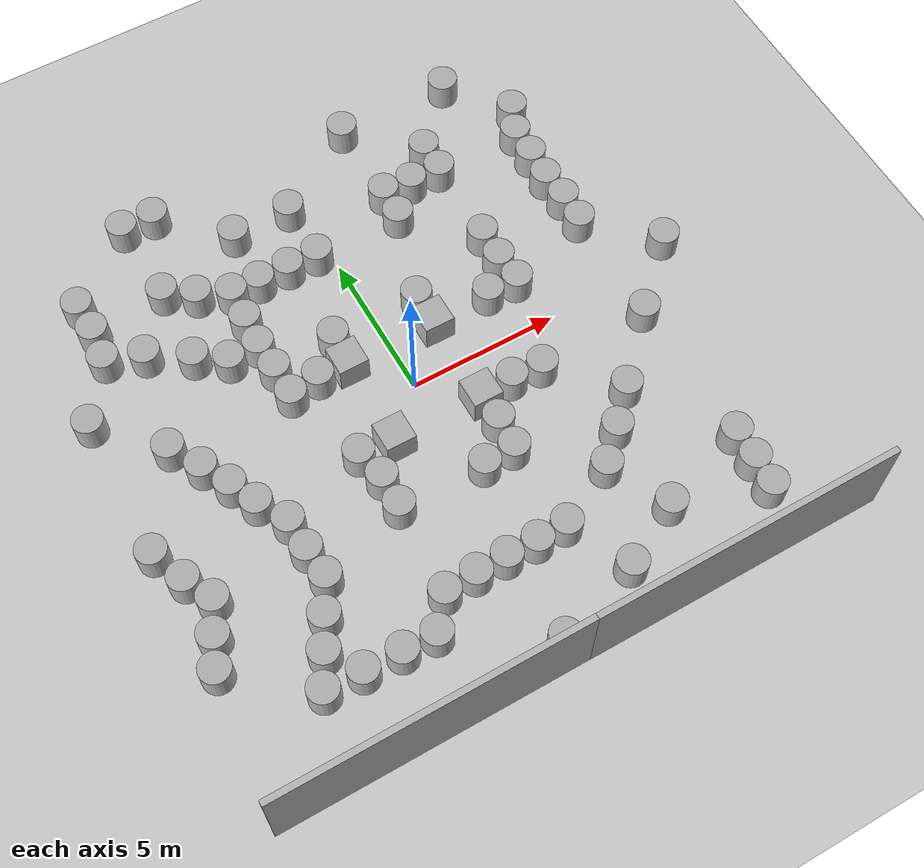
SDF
<sdf version="1.10">
 <world name="empty">
  <physics name="1ms" type="ignored">
   <max_step_size>0.001</max_step_size>
   <real_time_factor>1</real_time_factor>
   <real_time_update_rate>1000</real_time_update_rate>
  </physics>
  <plugin name="gz::sim::systems::Physics" filename="gz-sim-physics-system"/>
  <plugin name="gz::sim::systems::UserCommands" filename="gz-sim-user-commands-system"/>
  <plugin name="gz::sim::systems::SceneBroadcaster" filename="gz-sim-scene-broadcaster-system"/>
  <plugin name="gz::sim::systems::Contact" filename="gz-sim-contact-system"/>
  <gravity>0 0 -9.8000000000000007</gravity>
  <magnetic_field>5.5644999999999998e-06 2.2875799999999999e-05 -4.2388400000000002e-05</magnetic_field>
  <atmosphere type="adiabatic"/>
  <scene>
   <ambient>0.400000006 0.400000006 0.400000006 1</ambient>
   <background>0.699999988 0.699999988 0.699999988 1</background>
   <shadows>true</shadows>
  </scene>
  <model name="ground_plane">
   <static>true</static>
   <link name="link">
    <collision name="collision">
     <geometry><plane><normal>0 0 1</normal><size>100 100</size></plane></geometry>
    </collision>
    <visual name="visual">
     <geometry><plane><normal>0 0 1</normal><size>100 100</size></plane></geometry>
     <material>
      <ambient>0.800000012 0.800000012 0.800000012 1</ambient>
      <diffuse>0.800000012 0.800000012 0.800000012 1</diffuse>
      <specular>0.800000012 0.800000012 0.800000012 1</specular>
     </material>
    </visual>
    <inertial>
     <mass>1</mass>
     <inertia><ixx>1</ixx><ixy>0</ixy><ixz>0</ixz><iyy>1</iyy><iyz>0</iyz><izz>1</izz></inertia>
    </inertial>
   </link>
  </model>
  <model name="cutout_wall">
   <static>true</static>
   <link name="link">
    <pose>0 0 1.3999999999999999 0 0 0</pose>
    <collision name="collision">
     <geometry><box><size>10 0.20000000000000001 3.7999999999999998</size></box></geometry>
     <surface>
      <contact>
       <collide_without_contact>true</collide_without_contact>
       <collide_without_contact_bitmask>2</collide_without_contact_bitmask>
      </contact>
     </surface>
    </collision>
    <visual name="visual">
     <cast_shadows>false</cast_shadows>
     <geometry><box><size>10 0.20000000000000001 3.7999999999999998</size></box></geometry>
     <material>
      <script>
       <uri>https://fuel.gazebosim.org/1.0/openrobotics/models/cutout wall/2/files/materials/scripts</uri>
       <uri>https://fuel.gazebosim.org/1.0/openrobotics/models/cutout wall/2/files/materials/textures</uri>
       <name>drc_practice/cutout_wall</name>
      </script>
     </material>
    </visual>
    <sensor name="mud_contact" type="contact">
     <always_on>true</always_on>
     <update_rate>1000</update_rate>
     <contact><collision>collision</collision><topic>__default_topic__</topic></contact>
    </sensor>
    <inertial>
     <mass>1</mass>
     <inertia><ixx>1</ixx><ixy>0</ixy><ixz>0</ixz><iyy>1</iyy><iyz>0</iyz><izz>1</izz></inertia>
    </inertial>
   </link>
   <plugin name="gazebo_mud" filename="libMudPlugin.so">
    <contact_sensor_name>link/mud_contact</contact_sensor_name>
    <stiffness>0.0</stiffness>
    <damping>40.0</damping>
    <contact_surface_bitmask>2</contact_surface_bitmask>
    <link_name>drill::link</link_name>
   </plugin>
   <pose>5.0244002342224121 -10.112856864929199 0 0 0 0</pose>
  </model>
  <model name="cutout_wall_0">
   <static>true</static>
   <link name="link">
    <pose>0 0 1.3999999999999999 0 0 0</pose>
    <collision name="collision">
     <geometry><box><size>10 0.20000000000000001 3.7999999999999998</size></box></geometry>
     <surface>
      <contact>
       <collide_without_contact>true</collide_without_contact>
       <collide_without_contact_bitmask>2</collide_without_contact_bitmask>
      </contact>
     </surface>
    </collision>
    <visual name="visual">
     <cast_shadows>false</cast_shadows>
     <geometry><box><size>10 0.20000000000000001 3.7999999999999998</size></box></geometry>
     <material>
      <script>
       <uri>https://fuel.gazebosim.org/1.0/openrobotics/models/cutout wall/2/files/materials/scripts</uri>
       <uri>https://fuel.gazebosim.org/1.0/openrobotics/models/cutout wall/2/files/materials/textures</uri>
       <name>drc_practice/cutout_wall</name>
      </script>
     </material>
    </visual>
    <sensor name="mud_contact" type="contact">
     <always_on>true</always_on>
     <update_rate>1000</update_rate>
     <contact><collision>collision</collision><topic>__default_topic__</topic></contact>
    </sensor>
    <inertial>
     <mass>1</mass>
     <inertia><ixx>1</ixx><ixy>0</ixy><ixz>0</ixz><iyy>1</iyy><iyz>0</iyz><izz>1</izz></inertia>
    </inertial>
   </link>
   <plugin name="gazebo_mud" filename="libMudPlugin.so">
    <contact_sensor_name>link/mud_contact</contact_sensor_name>
    <stiffness>0.0</stiffness>
    <damping>40.0</damping>
    <contact_surface_bitmask>2</contact_surface_bitmask>
    <link_name>drill::link</link_name>
   </plugin>
   <pose>-4.9628870537703635 -10.110187173626739 0 0 0 0</pose>
  </model>
  <model name="box">
   <pose>-1.5142732858657837 1.5099300146102905 0.49999999990199806 8.6640958360379174e-21 4.2103315724608965e-23 5.9901372046615035e-22</pose>
   <link name="box_link">
    <inertial>
     <inertia><ixx>0.16666</ixx><ixy>0</ixy><ixz>0</ixz><iyy>0.16666</iyy><iyz>0</iyz><izz>0.16666</izz></inertia>
     <mass>1</mass>
    </inertial>
    <collision name="box_collision"><geometry><box><size>1 1 1</size></box></geometry></collision>
    <visual name="box_visual">
     <geometry><box><size>1 1 1</size></box></geometry>
     <material>
      <ambient>0.300000012 0.300000012 0.300000012 1</ambient>
      <diffuse>0.699999988 0.699999988 0.699999988 1</diffuse>
      <specular>1 1 1 1</specular>
     </material>
    </visual>
   </link>
   <static>false</static>
  </model>
  <model name="box_0">
   <pose>1.5080900192260742 1.5054577589035034 0.49999999990199806 9.9286448546489566e-22 -3.5225209775240119e-21 -3.9402750076948344e-22</pose>
   <link name="box_link">
    <inertial>
     <inertia><ixx>0.16666</ixx><ixy>0</ixy><ixz>0</ixz><iyy>0.16666</iyy><iyz>0</iyz><izz>0.16666</izz></inertia>
     <mass>1</mass>
    </inertial>
    <collision name="box_collision"><geometry><box><size>1 1 1</size></box></geometry></collision>
    <visual name="box_visual">
     <geometry><box><size>1 1 1</size></box></geometry>
     <material>
      <ambient>0.300000012 0.300000012 0.300000012 1</ambient>
      <diffuse>0.699999988 0.699999988 0.699999988 1</diffuse>
      <specular>1 1 1 1</specular>
     </material>
    </visual>
   </link>
   <static>false</static>
  </model>
  <model name="box_1">
   <pose>1.4997400045394897 -1.5082093477249146 0.49999999990199806 1.1517320518191673e-20 -1.1977566054568141e-20 -1.0673802548937443e-22</pose>
   <link name="box_link">
    <inertial>
     <inertia><ixx>0.16666</ixx><ixy>0</ixy><ixz>0</ixz><iyy>0.16666</iyy><iyz>0</iyz><izz>0.16666</izz></inertia>
     <mass>1</mass>
    </inertial>
    <collision name="box_collision"><geometry><box><size>1 1 1</size></box></geometry></collision>
    <visual name="box_visual">
     <geometry><box><size>1 1 1</size></box></geometry>
     <material>
      <ambient>0.300000012 0.300000012 0.300000012 1</ambient>
      <diffuse>0.699999988 0.699999988 0.699999988 1</diffuse>
      <specular>1 1 1 1</specular>
     </material>
    </visual>
   </link>
   <static>false</static>
  </model>
  <model name="box_2">
   <pose>-1.5103000402450562 -1.5050537586212158 0.49999999990199806 4.9253351279714187e-21 -3.9229219127948056e-21 -1.1103967100794144e-21</pose>
   <link name="box_link">
    <inertial>
     <inertia><ixx>0.16666</ixx><ixy>0</ixy><ixz>0</ixz><iyy>0.16666</iyy><iyz>0</iyz><izz>0.16666</izz></inertia>
     <mass>1</mass>
    </inertial>
    <collision name="box_collision"><geometry><box><size>1 1 1</size></box></geometry></collision>
    <visual name="box_visual">
     <geometry><box><size>1 1 1</size></box></geometry>
     <material>
      <ambient>0.300000012 0.300000012 0.300000012 1</ambient>
      <diffuse>0.699999988 0.699999988 0.699999988 1</diffuse>
      <specular>1 1 1 1</specular>
     </material>
    </visual>
   </link>
   <static>false</static>
  </model>
  <model name="cylinder">
   <pose>-1.4837546737511549 2.5115409236591981 0.49999942638036005 1.2900801804576693e-19 1.8421700609310675e-19 -1.4533065116624549e-20</pose>
   <link name="cylinder_link">
    <inertial>
     <inertia>
      <ixx>0.14580000000000001</ixx>
      <ixy>0</ixy>
      <ixz>0</ixz>
      <iyy>0.14580000000000001</iyy>
      <iyz>0</iyz>
      <izz>0.125</izz>
     </inertia>
     <mass>1</mass>
    </inertial>
    <collision name="cylinder_collision">
     <geometry><cylinder><radius>0.5</radius><length>1</length></cylinder></geometry>
    </collision>
    <visual name="cylinder_visual">
     <geometry><cylinder><radius>0.5</radius><length>1</length></cylinder></geometry>
     <material>
      <ambient>0.300000012 0.300000012 0.300000012 1</ambient>
      <diffuse>0.699999988 0.699999988 0.699999988 1</diffuse>
      <specular>1 1 1 1</specular>
     </material>
    </visual>
   </link>
   <static>false</static>
  </model>
  <model name="cylinder_0">
   <pose>-1.5368457435468508 5.5079104028776644 0.49999942638036005 -9.4769493904214775e-20 4.7750270177761677e-20 9.4196160317118267e-21</pose>
   <link name="cylinder_link">
    <inertial>
     <inertia>
      <ixx>0.14580000000000001</ixx>
      <ixy>0</ixy>
      <ixz>0</ixz>
      <iyy>0.14580000000000001</iyy>
      <iyz>0</iyz>
      <izz>0.125</izz>
     </inertia>
     <mass>1</mass>
    </inertial>
    <collision name="cylinder_collision">
     <geometry><cylinder><radius>0.5</radius><length>1</length></cylinder></geometry>
    </collision>
    <visual name="cylinder_visual">
     <geometry><cylinder><radius>0.5</radius><length>1</length></cylinder></geometry>
     <material>
      <ambient>0.300000012 0.300000012 0.300000012 1</ambient>
      <diffuse>0.699999988 0.699999988 0.699999988 1</diffuse>
      <specular>1 1 1 1</specular>
     </material>
    </visual>
   </link>
   <static>false</static>
  </model>
  <model name="cylinder_1">
   <pose>-0.50015280302760123 5.5109114429446704 0.49999942638036005 -1.8290064490072975e-19 -1.6022983802186347e-19 2.1797375953600389e-20</pose>
   <link name="cylinder_link">
    <inertial>
     <inertia>
      <ixx>0.14580000000000001</ixx>
      <ixy>0</ixy>
      <ixz>0</ixz>
      <iyy>0.14580000000000001</iyy>
      <iyz>0</iyz>
      <izz>0.125</izz>
     </inertia>
     <mass>1</mass>
    </inertial>
    <collision name="cylinder_collision">
     <geometry><cylinder><radius>0.5</radius><length>1</length></cylinder></geometry>
    </collision>
    <visual name="cylinder_visual">
     <geometry><cylinder><radius>0.5</radius><length>1</length></cylinder></geometry>
     <material>
      <ambient>0.300000012 0.300000012 0.300000012 1</ambient>
      <diffuse>0.699999988 0.699999988 0.699999988 1</diffuse>
      <specular>1 1 1 1</specular>
     </material>
    </visual>
   </link>
   <static>false</static>
  </model>
  <model name="cylinder_2">
   <pose>2.4653722738842641 5.5155461895708893 0.49999942638036005 -1.2159427297744482e-19 3.5312910165291729e-19 9.3546767268988265e-21</pose>
   <link name="cylinder_link">
    <inertial>
     <inertia>
      <ixx>0.14580000000000001</ixx>
      <ixy>0</ixy>
      <ixz>0</ixz>
      <iyy>0.14580000000000001</iyy>
      <iyz>0</iyz>
      <izz>0.125</izz>
     </inertia>
     <mass>1</mass>
    </inertial>
    <collision name="cylinder_collision">
     <geometry><cylinder><radius>0.5</radius><length>1</length></cylinder></geometry>
    </collision>
    <visual name="cylinder_visual">
     <geometry><cylinder><radius>0.5</radius><length>1</length></cylinder></geometry>
     <material>
      <ambient>0.300000012 0.300000012 0.300000012 1</ambient>
      <diffuse>0.699999988 0.699999988 0.699999988 1</diffuse>
      <specular>1 1 1 1</specular>
     </material>
    </visual>
   </link>
   <static>false</static>
  </model>
  <model name="cylinder_3">
   <pose>1.487433394811243 2.5255222043697376 0.49999942638036005 1.8706433839552678e-19 5.2283511329588628e-19 -1.3109912346937293e-21</pose>
   <link name="cylinder_link">
    <inertial>
     <inertia>
      <ixx>0.14580000000000001</ixx>
      <ixy>0</ixy>
      <ixz>0</ixz>
      <iyy>0.14580000000000001</iyy>
      <iyz>0</iyz>
      <izz>0.125</izz>
     </inertia>
     <mass>1</mass>
    </inertial>
    <collision name="cylinder_collision">
     <geometry><cylinder><radius>0.5</radius><length>1</length></cylinder></geometry>
    </collision>
    <visual name="cylinder_visual">
     <geometry><cylinder><radius>0.5</radius><length>1</length></cylinder></geometry>
     <material>
      <ambient>0.300000012 0.300000012 0.300000012 1</ambient>
      <diffuse>0.699999988 0.699999988 0.699999988 1</diffuse>
      <specular>1 1 1 1</specular>
     </material>
    </visual>
   </link>
   <static>false</static>
  </model>
  <model name="cylinder_4">
   <pose>2.4957145365909326 6.5562213824833719 0.49999942638036005 2.9988847440565745e-19 9.5693645168915657e-20 -8.4291119693885359e-22</pose>
   <link name="cylinder_link">
    <inertial>
     <inertia>
      <ixx>0.14580000000000001</ixx>
      <ixy>0</ixy>
      <ixz>0</ixz>
      <iyy>0.14580000000000001</iyy>
      <iyz>0</iyz>
      <izz>0.125</izz>
     </inertia>
     <mass>1</mass>
    </inertial>
    <collision name="cylinder_collision">
     <geometry><cylinder><radius>0.5</radius><length>1</length></cylinder></geometry>
    </collision>
    <visual name="cylinder_visual">
     <geometry><cylinder><radius>0.5</radius><length>1</length></cylinder></geometry>
     <material>
      <ambient>0.300000012 0.300000012 0.300000012 1</ambient>
      <diffuse>0.699999988 0.699999988 0.699999988 1</diffuse>
      <specular>1 1 1 1</specular>
     </material>
    </visual>
   </link>
   <static>false</static>
  </model>
  <model name="cylinder_5">
   <pose>2.5002937360492954 9.4833928405990733 0.49999942638036005 4.952361160460668e-19 4.8781056156440803e-20 -2.1634174162290521e-21</pose>
   <link name="cylinder_link">
    <inertial>
     <inertia>
      <ixx>0.14580000000000001</ixx>
      <ixy>0</ixy>
      <ixz>0</ixz>
      <iyy>0.14580000000000001</iyy>
      <iyz>0</iyz>
      <izz>0.125</izz>
     </inertia>
     <mass>1</mass>
    </inertial>
    <collision name="cylinder_collision">
     <geometry><cylinder><radius>0.5</radius><length>1</length></cylinder></geometry>
    </collision>
    <visual name="cylinder_visual">
     <geometry><cylinder><radius>0.5</radius><length>1</length></cylinder></geometry>
     <material>
      <ambient>0.300000012 0.300000012 0.300000012 1</ambient>
      <diffuse>0.699999988 0.699999988 0.699999988 1</diffuse>
      <specular>1 1 1 1</specular>
     </material>
    </visual>
   </link>
   <static>false</static>
  </model>
  <model name="cylinder_6">
   <pose>3.4993580008778014 6.4957876762254445 0.49999942638036005 -5.4248370582058287e-19 -1.5181386705707368e-19 2.4105179257938827e-20</pose>
   <link name="cylinder_link">
    <inertial>
     <inertia>
      <ixx>0.14580000000000001</ixx>
      <ixy>0</ixy>
      <ixz>0</ixz>
      <iyy>0.14580000000000001</iyy>
      <iyz>0</iyz>
      <izz>0.125</izz>
     </inertia>
     <mass>1</mass>
    </inertial>
    <collision name="cylinder_collision">
     <geometry><cylinder><radius>0.5</radius><length>1</length></cylinder></geometry>
    </collision>
    <visual name="cylinder_visual">
     <geometry><cylinder><radius>0.5</radius><length>1</length></cylinder></geometry>
     <material>
      <ambient>0.300000012 0.300000012 0.300000012 1</ambient>
      <diffuse>0.699999988 0.699999988 0.699999988 1</diffuse>
      <specular>1 1 1 1</specular>
     </material>
    </visual>
   </link>
   <static>false</static>
  </model>
  <model name="cylinder_7">
   <pose>-0.50707124966087003 7.5108884883755263 0.49999942638036005 -2.3858114257558744e-19 2.3553797688425662e-19 1.8040523486291411e-20</pose>
   <link name="cylinder_link">
    <inertial>
     <inertia>
      <ixx>0.14580000000000001</ixx>
      <ixy>0</ixy>
      <ixz>0</ixz>
      <iyy>0.14580000000000001</iyy>
      <iyz>0</iyz>
      <izz>0.125</izz>
     </inertia>
     <mass>1</mass>
    </inertial>
    <collision name="cylinder_collision">
     <geometry><cylinder><radius>0.5</radius><length>1</length></cylinder></geometry>
    </collision>
    <visual name="cylinder_visual">
     <geometry><cylinder><radius>0.5</radius><length>1</length></cylinder></geometry>
     <material>
      <ambient>0.300000012 0.300000012 0.300000012 1</ambient>
      <diffuse>0.699999988 0.699999988 0.699999988 1</diffuse>
      <specular>1 1 1 1</specular>
     </material>
    </visual>
   </link>
   <static>false</static>
  </model>
  <model name="cylinder_8">
   <pose>-2.4996507741781819 7.5008443332345465 0.49999942638036005 -1.6489635791491826e-19 9.8879298002299211e-20 4.3068522468604751e-21</pose>
   <link name="cylinder_link">
    <inertial>
     <inertia>
      <ixx>0.14580000000000001</ixx>
      <ixy>0</ixy>
      <ixz>0</ixz>
      <iyy>0.14580000000000001</iyy>
      <iyz>0</iyz>
      <izz>0.125</izz>
     </inertia>
     <mass>1</mass>
    </inertial>
    <collision name="cylinder_collision">
     <geometry><cylinder><radius>0.5</radius><length>1</length></cylinder></geometry>
    </collision>
    <visual name="cylinder_visual">
     <geometry><cylinder><radius>0.5</radius><length>1</length></cylinder></geometry>
     <material>
      <ambient>0.300000012 0.300000012 0.300000012 1</ambient>
      <diffuse>0.699999988 0.699999988 0.699999988 1</diffuse>
      <specular>1 1 1 1</specular>
     </material>
    </visual>
   </link>
   <static>false</static>
  </model>
  <model name="cylinder_9">
   <pose>-2.5696204517251955 5.5089517135262609 0.49999998400599954 -2.0713713632137981e-07 -4.9507126561741468e-07 3.8382690473443217e-06</pose>
   <link name="cylinder_link">
    <inertial>
     <inertia>
      <ixx>0.14580000000000001</ixx>
      <ixy>0</ixy>
      <ixz>0</ixz>
      <iyy>0.14580000000000001</iyy>
      <iyz>0</iyz>
      <izz>0.125</izz>
     </inertia>
     <mass>1</mass>
    </inertial>
    <collision name="cylinder_collision">
     <geometry><cylinder><radius>0.5</radius><length>1</length></cylinder></geometry>
    </collision>
    <visual name="cylinder_visual">
     <geometry><cylinder><radius>0.5</radius><length>1</length></cylinder></geometry>
     <material>
      <ambient>0.300000012 0.300000012 0.300000012 1</ambient>
      <diffuse>0.699999988 0.699999988 0.699999988 1</diffuse>
      <specular>1 1 1 1</specular>
     </material>
    </visual>
   </link>
   <static>false</static>
  </model>
  <model name="cylinder_10">
   <pose>4.4721789446645088 2.4781528318208035 0.49999942638036005 2.1119340590164374e-19 -1.2869265033623615e-19 2.1489386403418832e-20</pose>
   <link name="cylinder_link">
    <inertial>
     <inertia>
      <ixx>0.14580000000000001</ixx>
      <ixy>0</ixy>
      <ixz>0</ixz>
      <iyy>0.14580000000000001</iyy>
      <iyz>0</iyz>
      <izz>0.125</izz>
     </inertia>
     <mass>1</mass>
    </inertial>
    <collision name="cylinder_collision">
     <geometry><cylinder><radius>0.5</radius><length>1</length></cylinder></geometry>
    </collision>
    <visual name="cylinder_visual">
     <geometry><cylinder><radius>0.5</radius><length>1</length></cylinder></geometry>
     <material>
      <ambient>0.300000012 0.300000012 0.300000012 1</ambient>
      <diffuse>0.699999988 0.699999988 0.699999988 1</diffuse>
      <specular>1 1 1 1</specular>
     </material>
    </visual>
   </link>
   <static>false</static>
  </model>
  <model name="cylinder_11">
   <pose>3.5152813053362997 1.4995482606081814 0.49999943631074512 -1.8544028214068181e-10 -2.2052745795610097e-08 4.4973880338952816e-05</pose>
   <link name="cylinder_link">
    <inertial>
     <inertia>
      <ixx>0.14580000000000001</ixx>
      <ixy>0</ixy>
      <ixz>0</ixz>
      <iyy>0.14580000000000001</iyy>
      <iyz>0</iyz>
      <izz>0.125</izz>
     </inertia>
     <mass>1</mass>
    </inertial>
    <collision name="cylinder_collision">
     <geometry><cylinder><radius>0.5</radius><length>1</length></cylinder></geometry>
    </collision>
    <visual name="cylinder_visual">
     <geometry><cylinder><radius>0.5</radius><length>1</length></cylinder></geometry>
     <material>
      <ambient>0.300000012 0.300000012 0.300000012 1</ambient>
      <diffuse>0.699999988 0.699999988 0.699999988 1</diffuse>
      <specular>1 1 1 1</specular>
     </material>
    </visual>
   </link>
   <static>false</static>
  </model>
  <model name="cylinder_12">
   <pose>4.552820314980524 1.468549960563126 0.49999998219136932 -2.4499870759038959e-08 -7.8644388651687598e-07 3.3009431404225497e-07</pose>
   <link name="cylinder_link">
    <inertial>
     <inertia>
      <ixx>0.14580000000000001</ixx>
      <ixy>0</ixy>
      <ixz>0</ixz>
      <iyy>0.14580000000000001</iyy>
      <iyz>0</iyz>
      <izz>0.125</izz>
     </inertia>
     <mass>1</mass>
    </inertial>
    <collision name="cylinder_collision">
     <geometry><cylinder><radius>0.5</radius><length>1</length></cylinder></geometry>
    </collision>
    <visual name="cylinder_visual">
     <geometry><cylinder><radius>0.5</radius><length>1</length></cylinder></geometry>
     <material>
      <ambient>0.300000012 0.300000012 0.300000012 1</ambient>
      <diffuse>0.699999988 0.699999988 0.699999988 1</diffuse>
      <specular>1 1 1 1</specular>
     </material>
    </visual>
   </link>
   <static>false</static>
  </model>
  <model name="cylinder_13">
   <pose>4.489239547971648 3.5358175597300114 0.49999942638036005 2.8395949399691138e-20 1.5363331938510369e-19 1.5580847699489212e-21</pose>
   <link name="cylinder_link">
    <inertial>
     <inertia>
      <ixx>0.14580000000000001</ixx>
      <ixy>0</ixy>
      <ixz>0</ixz>
      <iyy>0.14580000000000001</iyy>
      <iyz>0</iyz>
      <izz>0.125</izz>
     </inertia>
     <mass>1</mass>
    </inertial>
    <collision name="cylinder_collision">
     <geometry><cylinder><radius>0.5</radius><length>1</length></cylinder></geometry>
    </collision>
    <visual name="cylinder_visual">
     <geometry><cylinder><radius>0.5</radius><length>1</length></cylinder></geometry>
     <material>
      <ambient>0.300000012 0.300000012 0.300000012 1</ambient>
      <diffuse>0.699999988 0.699999988 0.699999988 1</diffuse>
      <specular>1 1 1 1</specular>
     </material>
    </visual>
   </link>
   <static>false</static>
  </model>
  <model name="cylinder_14">
   <pose>4.5334383221910777 6.4630689108140515 0.49999935513131832 3.0144049288500607e-08 6.5836659992481903e-10 -1.4551269572321477e-06</pose>
   <link name="cylinder_link">
    <inertial>
     <inertia>
      <ixx>0.14580000000000001</ixx>
      <ixy>0</ixy>
      <ixz>0</ixz>
      <iyy>0.14580000000000001</iyy>
      <iyz>0</iyz>
      <izz>0.125</izz>
     </inertia>
     <mass>1</mass>
    </inertial>
    <collision name="cylinder_collision">
     <geometry><cylinder><radius>0.5</radius><length>1</length></cylinder></geometry>
    </collision>
    <visual name="cylinder_visual">
     <geometry><cylinder><radius>0.5</radius><length>1</length></cylinder></geometry>
     <material>
      <ambient>0.300000012 0.300000012 0.300000012 1</ambient>
      <diffuse>0.699999988 0.699999988 0.699999988 1</diffuse>
      <specular>1 1 1 1</specular>
     </material>
    </visual>
   </link>
   <static>false</static>
  </model>
  <model name="cylinder_15">
   <pose>7.4823215051992227 6.4945591897252086 0.49999942638036005 1.2455972657425889e-19 -1.3882705273865735e-19 -2.2267099675571353e-21</pose>
   <link name="cylinder_link">
    <inertial>
     <inertia>
      <ixx>0.14580000000000001</ixx>
      <ixy>0</ixy>
      <ixz>0</ixz>
      <iyy>0.14580000000000001</iyy>
      <iyz>0</iyz>
      <izz>0.125</izz>
     </inertia>
     <mass>1</mass>
    </inertial>
    <collision name="cylinder_collision">
     <geometry><cylinder><radius>0.5</radius><length>1</length></cylinder></geometry>
    </collision>
    <visual name="cylinder_visual">
     <geometry><cylinder><radius>0.5</radius><length>1</length></cylinder></geometry>
     <material>
      <ambient>0.300000012 0.300000012 0.300000012 1</ambient>
      <diffuse>0.699999988 0.699999988 0.699999988 1</diffuse>
      <specular>1 1 1 1</specular>
     </material>
    </visual>
   </link>
   <static>false</static>
  </model>
  <model name="cylinder_16">
   <pose>7.4717963036459176 5.4726410693874401 0.49999942638036005 -8.4782770555477578e-20 -2.2556734794786758e-19 -2.5207994231794371e-20</pose>
   <link name="cylinder_link">
    <inertial>
     <inertia>
      <ixx>0.14580000000000001</ixx>
      <ixy>0</ixy>
      <ixz>0</ixz>
      <iyy>0.14580000000000001</iyy>
      <iyz>0</iyz>
      <izz>0.125</izz>
     </inertia>
     <mass>1</mass>
    </inertial>
    <collision name="cylinder_collision">
     <geometry><cylinder><radius>0.5</radius><length>1</length></cylinder></geometry>
    </collision>
    <visual name="cylinder_visual">
     <geometry><cylinder><radius>0.5</radius><length>1</length></cylinder></geometry>
     <material>
      <ambient>0.300000012 0.300000012 0.300000012 1</ambient>
      <diffuse>0.699999988 0.699999988 0.699999988 1</diffuse>
      <specular>1 1 1 1</specular>
     </material>
    </visual>
   </link>
   <static>false</static>
  </model>
  <model name="cylinder_17">
   <pose>7.4234604183277808 4.4506516614444624 0.49999944074098934 -1.6028426987539136e-08 -2.4475236762986862e-08 -0.001658590448863326</pose>
   <link name="cylinder_link">
    <inertial>
     <inertia>
      <ixx>0.14580000000000001</ixx>
      <ixy>0</ixy>
      <ixz>0</ixz>
      <iyy>0.14580000000000001</iyy>
      <iyz>0</iyz>
      <izz>0.125</izz>
     </inertia>
     <mass>1</mass>
    </inertial>
    <collision name="cylinder_collision">
     <geometry><cylinder><radius>0.5</radius><length>1</length></cylinder></geometry>
    </collision>
    <visual name="cylinder_visual">
     <geometry><cylinder><radius>0.5</radius><length>1</length></cylinder></geometry>
     <material>
      <ambient>0.300000012 0.300000012 0.300000012 1</ambient>
      <diffuse>0.699999988 0.699999988 0.699999988 1</diffuse>
      <specular>1 1 1 1</specular>
     </material>
    </visual>
   </link>
   <static>false</static>
  </model>
  <model name="cylinder_18">
   <pose>4.5210768934154846 7.4629925688739567 0.49999944205754038 3.3042527129199502e-08 1.2918855681529939e-10 -1.7726808627645601e-07</pose>
   <link name="cylinder_link">
    <inertial>
     <inertia>
      <ixx>0.14580000000000001</ixx>
      <ixy>0</ixy>
      <ixz>0</ixz>
      <iyy>0.14580000000000001</iyy>
      <iyz>0</iyz>
      <izz>0.125</izz>
     </inertia>
     <mass>1</mass>
    </inertial>
    <collision name="cylinder_collision">
     <geometry><cylinder><radius>0.5</radius><length>1</length></cylinder></geometry>
    </collision>
    <visual name="cylinder_visual">
     <geometry><cylinder><radius>0.5</radius><length>1</length></cylinder></geometry>
     <material>
      <ambient>0.300000012 0.300000012 0.300000012 1</ambient>
      <diffuse>0.699999988 0.699999988 0.699999988 1</diffuse>
      <specular>1 1 1 1</specular>
     </material>
    </visual>
   </link>
   <static>false</static>
  </model>
  <model name="cylinder_19">
   <pose>6.3855396230830648 9.4949946010721771 0.49999943518614837 2.0141951548457427e-08 3.012327523038749e-19 2.3956164309829781e-17</pose>
   <link name="cylinder_link">
    <inertial>
     <inertia>
      <ixx>0.14580000000000001</ixx>
      <ixy>0</ixy>
      <ixz>0</ixz>
      <iyy>0.14580000000000001</iyy>
      <iyz>0</iyz>
      <izz>0.125</izz>
     </inertia>
     <mass>1</mass>
    </inertial>
    <collision name="cylinder_collision">
     <geometry><cylinder><radius>0.5</radius><length>1</length></cylinder></geometry>
    </collision>
    <visual name="cylinder_visual">
     <geometry><cylinder><radius>0.5</radius><length>1</length></cylinder></geometry>
     <material>
      <ambient>0.300000012 0.300000012 0.300000012 1</ambient>
      <diffuse>0.699999988 0.699999988 0.699999988 1</diffuse>
      <specular>1 1 1 1</specular>
     </material>
    </visual>
   </link>
   <static>false</static>
  </model>
  <model name="cylinder_20">
   <pose>7.9166001046539822 7.4447277907300071 0.49999942638036005 -6.0129972703811341e-20 -3.6477302982958059e-19 1.2185579178527888e-20</pose>
   <link name="cylinder_link">
    <inertial>
     <inertia>
      <ixx>0.14580000000000001</ixx>
      <ixy>0</ixy>
      <ixz>0</ixz>
      <iyy>0.14580000000000001</iyy>
      <iyz>0</iyz>
      <izz>0.125</izz>
     </inertia>
     <mass>1</mass>
    </inertial>
    <collision name="cylinder_collision">
     <geometry><cylinder><radius>0.5</radius><length>1</length></cylinder></geometry>
    </collision>
    <visual name="cylinder_visual">
     <geometry><cylinder><radius>0.5</radius><length>1</length></cylinder></geometry>
     <material>
      <ambient>0.300000012 0.300000012 0.300000012 1</ambient>
      <diffuse>0.699999988 0.699999988 0.699999988 1</diffuse>
      <specular>1 1 1 1</specular>
     </material>
    </visual>
   </link>
   <static>false</static>
  </model>
  <model name="cylinder_21">
   <pose>7.4979118562813794 3.4534278174375852 0.49999942639754313 7.3099042971253039e-11 2.3369477153850155e-09 -0.0028957251323138439</pose>
   <link name="cylinder_link">
    <inertial>
     <inertia>
      <ixx>0.14580000000000001</ixx>
      <ixy>0</ixy>
      <ixz>0</ixz>
      <iyy>0.14580000000000001</iyy>
      <iyz>0</iyz>
      <izz>0.125</izz>
     </inertia>
     <mass>1</mass>
    </inertial>
    <collision name="cylinder_collision">
     <geometry><cylinder><radius>0.5</radius><length>1</length></cylinder></geometry>
    </collision>
    <visual name="cylinder_visual">
     <geometry><cylinder><radius>0.5</radius><length>1</length></cylinder></geometry>
     <material>
      <ambient>0.300000012 0.300000012 0.300000012 1</ambient>
      <diffuse>0.699999988 0.699999988 0.699999988 1</diffuse>
      <specular>1 1 1 1</specular>
     </material>
    </visual>
   </link>
   <static>false</static>
  </model>
  <model name="cylinder_22">
   <pose>7.4863467383450555 2.453493927277647 0.49999943589273554 2.3672179419543697e-08 -2.0984223274804382e-09 1.9708317345152628e-06</pose>
   <link name="cylinder_link">
    <inertial>
     <inertia>
      <ixx>0.14580000000000001</ixx>
      <ixy>0</ixy>
      <ixz>0</ixz>
      <iyy>0.14580000000000001</iyy>
      <iyz>0</iyz>
      <izz>0.125</izz>
     </inertia>
     <mass>1</mass>
    </inertial>
    <collision name="cylinder_collision">
     <geometry><cylinder><radius>0.5</radius><length>1</length></cylinder></geometry>
    </collision>
    <visual name="cylinder_visual">
     <geometry><cylinder><radius>0.5</radius><length>1</length></cylinder></geometry>
     <material>
      <ambient>0.300000012 0.300000012 0.300000012 1</ambient>
      <diffuse>0.699999988 0.699999988 0.699999988 1</diffuse>
      <specular>1 1 1 1</specular>
     </material>
    </visual>
   </link>
   <static>false</static>
  </model>
  <model name="cylinder_23">
   <pose>9.4865532197129454 0.51658195677780983 0.49999943519489742 -3.3591824192756615e-09 -2.0134794209095349e-08 3.0046556169471104e-05</pose>
   <link name="cylinder_link">
    <inertial>
     <inertia>
      <ixx>0.14580000000000001</ixx>
      <ixy>0</ixy>
      <ixz>0</ixz>
      <iyy>0.14580000000000001</iyy>
      <iyz>0</iyz>
      <izz>0.125</izz>
     </inertia>
     <mass>1</mass>
    </inertial>
    <collision name="cylinder_collision">
     <geometry><cylinder><radius>0.5</radius><length>1</length></cylinder></geometry>
    </collision>
    <visual name="cylinder_visual">
     <geometry><cylinder><radius>0.5</radius><length>1</length></cylinder></geometry>
     <material>
      <ambient>0.300000012 0.300000012 0.300000012 1</ambient>
      <diffuse>0.699999988 0.699999988 0.699999988 1</diffuse>
      <specular>1 1 1 1</specular>
     </material>
    </visual>
   </link>
   <static>false</static>
  </model>
  <model name="cylinder_24">
   <pose>7.4579679743214129 -1.4635169595611899 0.49999942638036005 1.0404121543791637e-19 3.6597615079895941e-20 1.8234863927649828e-20</pose>
   <link name="cylinder_link">
    <inertial>
     <inertia>
      <ixx>0.14580000000000001</ixx>
      <ixy>0</ixy>
      <ixz>0</ixz>
      <iyy>0.14580000000000001</iyy>
      <iyz>0</iyz>
      <izz>0.125</izz>
     </inertia>
     <mass>1</mass>
    </inertial>
    <collision name="cylinder_collision">
     <geometry><cylinder><radius>0.5</radius><length>1</length></cylinder></geometry>
    </collision>
    <visual name="cylinder_visual">
     <geometry><cylinder><radius>0.5</radius><length>1</length></cylinder></geometry>
     <material>
      <ambient>0.300000012 0.300000012 0.300000012 1</ambient>
      <diffuse>0.699999988 0.699999988 0.699999988 1</diffuse>
      <specular>1 1 1 1</specular>
     </material>
    </visual>
   </link>
   <static>false</static>
  </model>
  <model name="cylinder_25">
   <pose>5.5018903763678519 -3.4989337276191517 0.49999942638036005 1.4860132144114843e-19 1.7661039450246635e-19 4.0893450691587339e-21</pose>
   <link name="cylinder_link">
    <inertial>
     <inertia>
      <ixx>0.14580000000000001</ixx>
      <ixy>0</ixy>
      <ixz>0</ixz>
      <iyy>0.14580000000000001</iyy>
      <iyz>0</iyz>
      <izz>0.125</izz>
     </inertia>
     <mass>1</mass>
    </inertial>
    <collision name="cylinder_collision">
     <geometry><cylinder><radius>0.5</radius><length>1</length></cylinder></geometry>
    </collision>
    <visual name="cylinder_visual">
     <geometry><cylinder><radius>0.5</radius><length>1</length></cylinder></geometry>
     <material>
      <ambient>0.300000012 0.300000012 0.300000012 1</ambient>
      <diffuse>0.699999988 0.699999988 0.699999988 1</diffuse>
      <specular>1 1 1 1</specular>
     </material>
    </visual>
   </link>
   <static>false</static>
  </model>
  <model name="cylinder_26">
   <pose>7.4913997650146484 -6.4739174842834473 0.49999899681693183 -1.6107873630028886e-19 -1.3158036878917675e-19 -6.9647624872487262e-21</pose>
   <link name="cylinder_link">
    <inertial>
     <inertia>
      <ixx>0.14580000000000001</ixx>
      <ixy>0</ixy>
      <ixz>0</ixz>
      <iyy>0.14580000000000001</iyy>
      <iyz>0</iyz>
      <izz>0.125</izz>
     </inertia>
     <mass>1</mass>
    </inertial>
    <collision name="cylinder_collision">
     <geometry><cylinder><radius>0.5</radius><length>1</length></cylinder></geometry>
    </collision>
    <visual name="cylinder_visual">
     <geometry><cylinder><radius>0.5</radius><length>1</length></cylinder></geometry>
     <material>
      <ambient>0.300000012 0.300000012 0.300000012 1</ambient>
      <diffuse>0.699999988 0.699999988 0.699999988 1</diffuse>
      <specular>1 1 1 1</specular>
     </material>
    </visual>
   </link>
   <static>false</static>
  </model>
  <model name="cylinder_27">
   <pose>4.5036947868113426 -7.4734161285770995 0.49999942638036005 4.5825536641846892e-19 -7.7492820516809437e-20 7.7745020133747469e-21</pose>
   <link name="cylinder_link">
    <inertial>
     <inertia>
      <ixx>0.14580000000000001</ixx>
      <ixy>0</ixy>
      <ixz>0</ixz>
      <iyy>0.14580000000000001</iyy>
      <iyz>0</iyz>
      <izz>0.125</izz>
     </inertia>
     <mass>1</mass>
    </inertial>
    <collision name="cylinder_collision">
     <geometry><cylinder><radius>0.5</radius><length>1</length></cylinder></geometry>
    </collision>
    <visual name="cylinder_visual">
     <geometry><cylinder><radius>0.5</radius><length>1</length></cylinder></geometry>
     <material>
      <ambient>0.300000012 0.300000012 0.300000012 1</ambient>
      <diffuse>0.699999988 0.699999988 0.699999988 1</diffuse>
      <specular>1 1 1 1</specular>
     </material>
    </visual>
   </link>
   <static>false</static>
  </model>
  <model name="cylinder_28">
   <pose>7.404863327792464 -8.4644145675349485 0.49999997297122245 -3.5262700033126905e-07 1.4435802526447565e-07 0.00094128847841023924</pose>
   <link name="cylinder_link">
    <inertial>
     <inertia>
      <ixx>0.14580000000000001</ixx>
      <ixy>0</ixy>
      <ixz>0</ixz>
      <iyy>0.14580000000000001</iyy>
      <iyz>0</iyz>
      <izz>0.125</izz>
     </inertia>
     <mass>1</mass>
    </inertial>
    <collision name="cylinder_collision">
     <geometry><cylinder><radius>0.5</radius><length>1</length></cylinder></geometry>
    </collision>
    <visual name="cylinder_visual">
     <geometry><cylinder><radius>0.5</radius><length>1</length></cylinder></geometry>
     <material>
      <ambient>0.300000012 0.300000012 0.300000012 1</ambient>
      <diffuse>0.699999988 0.699999988 0.699999988 1</diffuse>
      <specular>1 1 1 1</specular>
     </material>
    </visual>
   </link>
   <static>false</static>
  </model>
  <model name="cylinder_29">
   <pose>7.4653034075764992 -7.4820488905984313 0.49999414175929674 -2.6838842488045363e-06 -4.6486356529296626e-07 0.0016932280995456796</pose>
   <link name="cylinder_link">
    <inertial>
     <inertia>
      <ixx>0.14580000000000001</ixx>
      <ixy>0</ixy>
      <ixz>0</ixz>
      <iyy>0.14580000000000001</iyy>
      <iyz>0</iyz>
      <izz>0.125</izz>
     </inertia>
     <mass>1</mass>
    </inertial>
    <collision name="cylinder_collision">
     <geometry><cylinder><radius>0.5</radius><length>1</length></cylinder></geometry>
    </collision>
    <visual name="cylinder_visual">
     <geometry><cylinder><radius>0.5</radius><length>1</length></cylinder></geometry>
     <material>
      <ambient>0.300000012 0.300000012 0.300000012 1</ambient>
      <diffuse>0.699999988 0.699999988 0.699999988 1</diffuse>
      <specular>1 1 1 1</specular>
     </material>
    </visual>
   </link>
   <static>false</static>
  </model>
  <model name="cylinder_30">
   <pose>3.5181975875642597 -5.4882700601763243 0.49999942638036005 -9.0263386896251064e-20 1.227965443005862e-19 -6.4139063919702918e-21</pose>
   <link name="cylinder_link">
    <inertial>
     <inertia>
      <ixx>0.14580000000000001</ixx>
      <ixy>0</ixy>
      <ixz>0</ixz>
      <iyy>0.14580000000000001</iyy>
      <iyz>0</iyz>
      <izz>0.125</izz>
     </inertia>
     <mass>1</mass>
    </inertial>
    <collision name="cylinder_collision">
     <geometry><cylinder><radius>0.5</radius><length>1</length></cylinder></geometry>
    </collision>
    <visual name="cylinder_visual">
     <geometry><cylinder><radius>0.5</radius><length>1</length></cylinder></geometry>
     <material>
      <ambient>0.300000012 0.300000012 0.300000012 1</ambient>
      <diffuse>0.699999988 0.699999988 0.699999988 1</diffuse>
      <specular>1 1 1 1</specular>
     </material>
    </visual>
   </link>
   <static>false</static>
  </model>
  <model name="cylinder_31">
   <pose>2.4567228461091841 -8.5414870793526454 0.49999942638036005 2.5504988768588672e-19 6.5733350619232242e-20 -5.8407872868714071e-21</pose>
   <link name="cylinder_link">
    <inertial>
     <inertia>
      <ixx>0.14580000000000001</ixx>
      <ixy>0</ixy>
      <ixz>0</ixz>
      <iyy>0.14580000000000001</iyy>
      <iyz>0</iyz>
      <izz>0.125</izz>
     </inertia>
     <mass>1</mass>
    </inertial>
    <collision name="cylinder_collision">
     <geometry><cylinder><radius>0.5</radius><length>1</length></cylinder></geometry>
    </collision>
    <visual name="cylinder_visual">
     <geometry><cylinder><radius>0.5</radius><length>1</length></cylinder></geometry>
     <material>
      <ambient>0.300000012 0.300000012 0.300000012 1</ambient>
      <diffuse>0.699999988 0.699999988 0.699999988 1</diffuse>
      <specular>1 1 1 1</specular>
     </material>
    </visual>
   </link>
   <static>false</static>
  </model>
  <model name="cylinder_32">
   <pose>1.4836808308464846 -6.5152958040956168 0.49999942638036005 1.8706455609397484e-19 -4.394916380758869e-19 6.1073173625950871e-21</pose>
   <link name="cylinder_link">
    <inertial>
     <inertia>
      <ixx>0.14580000000000001</ixx>
      <ixy>0</ixy>
      <ixz>0</ixz>
      <iyy>0.14580000000000001</iyy>
      <iyz>0</iyz>
      <izz>0.125</izz>
     </inertia>
     <mass>1</mass>
    </inertial>
    <collision name="cylinder_collision">
     <geometry><cylinder><radius>0.5</radius><length>1</length></cylinder></geometry>
    </collision>
    <visual name="cylinder_visual">
     <geometry><cylinder><radius>0.5</radius><length>1</length></cylinder></geometry>
     <material>
      <ambient>0.300000012 0.300000012 0.300000012 1</ambient>
      <diffuse>0.699999988 0.699999988 0.699999988 1</diffuse>
      <specular>1 1 1 1</specular>
     </material>
    </visual>
   </link>
   <static>false</static>
  </model>
  <model name="cylinder_33">
   <pose>1.4988005276540712 -2.5632170485841277 0.49999942638036005 1.1352717714565005e-19 1.3222497010475083e-19 1.2599571809446981e-20</pose>
   <link name="cylinder_link">
    <inertial>
     <inertia>
      <ixx>0.14580000000000001</ixx>
      <ixy>0</ixy>
      <ixz>0</ixz>
      <iyy>0.14580000000000001</iyy>
      <iyz>0</iyz>
      <izz>0.125</izz>
     </inertia>
     <mass>1</mass>
    </inertial>
    <collision name="cylinder_collision">
     <geometry><cylinder><radius>0.5</radius><length>1</length></cylinder></geometry>
    </collision>
    <visual name="cylinder_visual">
     <geometry><cylinder><radius>0.5</radius><length>1</length></cylinder></geometry>
     <material>
      <ambient>0.300000012 0.300000012 0.300000012 1</ambient>
      <diffuse>0.699999988 0.699999988 0.699999988 1</diffuse>
      <specular>1 1 1 1</specular>
     </material>
    </visual>
   </link>
   <static>false</static>
  </model>
  <model name="cylinder_34">
   <pose>2.5982537141017641 -1.5151636730561524 0.49999942638036005 -1.7351388523841535e-19 5.5625022594761692e-20 -2.5965143220246563e-21</pose>
   <link name="cylinder_link">
    <inertial>
     <inertia>
      <ixx>0.14580000000000001</ixx>
      <ixy>0</ixy>
      <ixz>0</ixz>
      <iyy>0.14580000000000001</iyy>
      <iyz>0</iyz>
      <izz>0.125</izz>
     </inertia>
     <mass>1</mass>
    </inertial>
    <collision name="cylinder_collision">
     <geometry><cylinder><radius>0.5</radius><length>1</length></cylinder></geometry>
    </collision>
    <visual name="cylinder_visual">
     <geometry><cylinder><radius>0.5</radius><length>1</length></cylinder></geometry>
     <material>
      <ambient>0.300000012 0.300000012 0.300000012 1</ambient>
      <diffuse>0.699999988 0.699999988 0.699999988 1</diffuse>
      <specular>1 1 1 1</specular>
     </material>
    </visual>
   </link>
   <static>false</static>
  </model>
  <model name="cylinder_35">
   <pose>3.6352396272639154 -1.5871415900589758 0.49999942638036005 2.7912113488755255e-19 2.3054390331751714e-19 -1.371123595140014e-20</pose>
   <link name="cylinder_link">
    <inertial>
     <inertia>
      <ixx>0.14580000000000001</ixx>
      <ixy>0</ixy>
      <ixz>0</ixz>
      <iyy>0.14580000000000001</iyy>
      <iyz>0</iyz>
      <izz>0.125</izz>
     </inertia>
     <mass>1</mass>
    </inertial>
    <collision name="cylinder_collision">
     <geometry><cylinder><radius>0.5</radius><length>1</length></cylinder></geometry>
    </collision>
    <visual name="cylinder_visual">
     <geometry><cylinder><radius>0.5</radius><length>1</length></cylinder></geometry>
     <material>
      <ambient>0.300000012 0.300000012 0.300000012 1</ambient>
      <diffuse>0.699999988 0.699999988 0.699999988 1</diffuse>
      <specular>1 1 1 1</specular>
     </material>
    </visual>
   </link>
   <static>false</static>
  </model>
  <model name="cylinder_36">
   <pose>4.4832683135535412 -4.5509423094535553 0.49999942638036005 7.2649451183577797e-20 -4.8473965762629511e-20 7.0300260481472819e-21</pose>
   <link name="cylinder_link">
    <inertial>
     <inertia>
      <ixx>0.14580000000000001</ixx>
      <ixy>0</ixy>
      <ixz>0</ixz>
      <iyy>0.14580000000000001</iyy>
      <iyz>0</iyz>
      <izz>0.125</izz>
     </inertia>
     <mass>1</mass>
    </inertial>
    <collision name="cylinder_collision">
     <geometry><cylinder><radius>0.5</radius><length>1</length></cylinder></geometry>
    </collision>
    <visual name="cylinder_visual">
     <geometry><cylinder><radius>0.5</radius><length>1</length></cylinder></geometry>
     <material>
      <ambient>0.300000012 0.300000012 0.300000012 1</ambient>
      <diffuse>0.699999988 0.699999988 0.699999988 1</diffuse>
      <specular>1 1 1 1</specular>
     </material>
    </visual>
   </link>
   <static>false</static>
  </model>
  <model name="cylinder_37">
   <pose>1.4318604379295714 -3.6028194224507994 0.49999942638036005 7.4099042318196404e-20 5.5378451692048979e-20 -1.2954720819263041e-20</pose>
   <link name="cylinder_link">
    <inertial>
     <inertia>
      <ixx>0.14580000000000001</ixx>
      <ixy>0</ixy>
      <ixz>0</ixz>
      <iyy>0.14580000000000001</iyy>
      <iyz>0</iyz>
      <izz>0.125</izz>
     </inertia>
     <mass>1</mass>
    </inertial>
    <collision name="cylinder_collision">
     <geometry><cylinder><radius>0.5</radius><length>1</length></cylinder></geometry>
    </collision>
    <visual name="cylinder_visual">
     <geometry><cylinder><radius>0.5</radius><length>1</length></cylinder></geometry>
     <material>
      <ambient>0.300000012 0.300000012 0.300000012 1</ambient>
      <diffuse>0.699999988 0.699999988 0.699999988 1</diffuse>
      <specular>1 1 1 1</specular>
     </material>
    </visual>
   </link>
   <static>false</static>
  </model>
  <model name="cylinder_38">
   <pose>0.4701120445519768 -6.5480743106443633 0.49999942638036005 4.1439297792588681e-19 4.8641858540403024e-19 2.7303903312444181e-20</pose>
   <link name="cylinder_link">
    <inertial>
     <inertia>
      <ixx>0.14580000000000001</ixx>
      <ixy>0</ixy>
      <ixz>0</ixz>
      <iyy>0.14580000000000001</iyy>
      <iyz>0</iyz>
      <izz>0.125</izz>
     </inertia>
     <mass>1</mass>
    </inertial>
    <collision name="cylinder_collision">
     <geometry><cylinder><radius>0.5</radius><length>1</length></cylinder></geometry>
    </collision>
    <visual name="cylinder_visual">
     <geometry><cylinder><radius>0.5</radius><length>1</length></cylinder></geometry>
     <material>
      <ambient>0.300000012 0.300000012 0.300000012 1</ambient>
      <diffuse>0.699999988 0.699999988 0.699999988 1</diffuse>
      <specular>1 1 1 1</specular>
     </material>
    </visual>
   </link>
   <static>false</static>
  </model>
  <model name="cylinder_39">
   <pose>-0.39289321029540758 -9.4703206059036553 0.49999942638036005 -1.0612329675700295e-19 -3.1560568702048225e-19 6.0230042435980867e-21</pose>
   <link name="cylinder_link">
    <inertial>
     <inertia>
      <ixx>0.14580000000000001</ixx>
      <ixy>0</ixy>
      <ixz>0</ixz>
      <iyy>0.14580000000000001</iyy>
      <iyz>0</iyz>
      <izz>0.125</izz>
     </inertia>
     <mass>1</mass>
    </inertial>
    <collision name="cylinder_collision">
     <geometry><cylinder><radius>0.5</radius><length>1</length></cylinder></geometry>
    </collision>
    <visual name="cylinder_visual">
     <geometry><cylinder><radius>0.5</radius><length>1</length></cylinder></geometry>
     <material>
      <ambient>0.300000012 0.300000012 0.300000012 1</ambient>
      <diffuse>0.699999988 0.699999988 0.699999988 1</diffuse>
      <specular>1 1 1 1</specular>
     </material>
    </visual>
   </link>
   <static>false</static>
  </model>
  <model name="cylinder_40">
   <pose>-0.55864247399234923 -6.5343551494490271 0.49999942638036005 4.0541481752841836e-19 -1.7716716103474124e-19 -8.9936384247304861e-21</pose>
   <link name="cylinder_link">
    <inertial>
     <inertia>
      <ixx>0.14580000000000001</ixx>
      <ixy>0</ixy>
      <ixz>0</ixz>
      <iyy>0.14580000000000001</iyy>
      <iyz>0</iyz>
      <izz>0.125</izz>
     </inertia>
     <mass>1</mass>
    </inertial>
    <collision name="cylinder_collision">
     <geometry><cylinder><radius>0.5</radius><length>1</length></cylinder></geometry>
    </collision>
    <visual name="cylinder_visual">
     <geometry><cylinder><radius>0.5</radius><length>1</length></cylinder></geometry>
     <material>
      <ambient>0.300000012 0.300000012 0.300000012 1</ambient>
      <diffuse>0.699999988 0.699999988 0.699999988 1</diffuse>
      <specular>1 1 1 1</specular>
     </material>
    </visual>
   </link>
   <static>false</static>
  </model>
  <model name="cylinder_41">
   <pose>-1.5909876523756719 -6.549522709019417 0.49999942638036005 -2.723644736422706e-19 -4.2175234747128296e-20 1.0337401582250631e-20</pose>
   <link name="cylinder_link">
    <inertial>
     <inertia>
      <ixx>0.14580000000000001</ixx>
      <ixy>0</ixy>
      <ixz>0</ixz>
      <iyy>0.14580000000000001</iyy>
      <iyz>0</iyz>
      <izz>0.125</izz>
     </inertia>
     <mass>1</mass>
    </inertial>
    <collision name="cylinder_collision">
     <geometry><cylinder><radius>0.5</radius><length>1</length></cylinder></geometry>
    </collision>
    <visual name="cylinder_visual">
     <geometry><cylinder><radius>0.5</radius><length>1</length></cylinder></geometry>
     <material>
      <ambient>0.300000012 0.300000012 0.300000012 1</ambient>
      <diffuse>0.699999988 0.699999988 0.699999988 1</diffuse>
      <specular>1 1 1 1</specular>
     </material>
    </visual>
   </link>
   <static>false</static>
  </model>
  <model name="cylinder_42">
   <pose>-2.6606234614555997 -6.604773553741321 0.49999942638036005 2.7798991432306755e-19 -2.6032469691397042e-19 2.1424046912927031e-20</pose>
   <link name="cylinder_link">
    <inertial>
     <inertia>
      <ixx>0.14580000000000001</ixx>
      <ixy>0</ixy>
      <ixz>0</ixz>
      <iyy>0.14580000000000001</iyy>
      <iyz>0</iyz>
      <izz>0.125</izz>
     </inertia>
     <mass>1</mass>
    </inertial>
    <collision name="cylinder_collision">
     <geometry><cylinder><radius>0.5</radius><length>1</length></cylinder></geometry>
    </collision>
    <visual name="cylinder_visual">
     <geometry><cylinder><radius>0.5</radius><length>1</length></cylinder></geometry>
     <material>
      <ambient>0.300000012 0.300000012 0.300000012 1</ambient>
      <diffuse>0.699999988 0.699999988 0.699999988 1</diffuse>
      <specular>1 1 1 1</specular>
     </material>
    </visual>
   </link>
   <static>false</static>
  </model>
  <model name="cylinder_43">
   <pose>-3.4618544785568299 -7.5837527019556656 0.49999942638036005 1.420435048148452e-19 -8.7965788570413045e-20 1.8581114252052647e-20</pose>
   <link name="cylinder_link">
    <inertial>
     <inertia>
      <ixx>0.14580000000000001</ixx>
      <ixy>0</ixy>
      <ixz>0</ixz>
      <iyy>0.14580000000000001</iyy>
      <iyz>0</iyz>
      <izz>0.125</izz>
     </inertia>
     <mass>1</mass>
    </inertial>
    <collision name="cylinder_collision">
     <geometry><cylinder><radius>0.5</radius><length>1</length></cylinder></geometry>
    </collision>
    <visual name="cylinder_visual">
     <geometry><cylinder><radius>0.5</radius><length>1</length></cylinder></geometry>
     <material>
      <ambient>0.300000012 0.300000012 0.300000012 1</ambient>
      <diffuse>0.699999988 0.699999988 0.699999988 1</diffuse>
      <specular>1 1 1 1</specular>
     </material>
    </visual>
   </link>
   <static>false</static>
  </model>
  <model name="cylinder_45">
   <pose>-7.0212748879467828 -7.4850845913170003 0.49999942638036005 -2.4974064668848351e-19 -4.4274681889498242e-19 -1.5337513425931116e-20</pose>
   <link name="cylinder_link">
    <inertial>
     <inertia>
      <ixx>0.14580000000000001</ixx>
      <ixy>0</ixy>
      <ixz>0</ixz>
      <iyy>0.14580000000000001</iyy>
      <iyz>0</iyz>
      <izz>0.125</izz>
     </inertia>
     <mass>1</mass>
    </inertial>
    <collision name="cylinder_collision">
     <geometry><cylinder><radius>0.5</radius><length>1</length></cylinder></geometry>
    </collision>
    <visual name="cylinder_visual">
     <geometry><cylinder><radius>0.5</radius><length>1</length></cylinder></geometry>
     <material>
      <ambient>0.300000012 0.300000012 0.300000012 1</ambient>
      <diffuse>0.699999988 0.699999988 0.699999988 1</diffuse>
      <specular>1 1 1 1</specular>
     </material>
    </visual>
   </link>
   <static>false</static>
  </model>
  <model name="cylinder_46">
   <pose>-6.4831823274444051 -6.4902933339226037 0.49999942638036005 1.0849121461906336e-20 -2.3015827358014971e-19 1.7966367658804048e-20</pose>
   <link name="cylinder_link">
    <inertial>
     <inertia>
      <ixx>0.14580000000000001</ixx>
      <ixy>0</ixy>
      <ixz>0</ixz>
      <iyy>0.14580000000000001</iyy>
      <iyz>0</iyz>
      <izz>0.125</izz>
     </inertia>
     <mass>1</mass>
    </inertial>
    <collision name="cylinder_collision">
     <geometry><cylinder><radius>0.5</radius><length>1</length></cylinder></geometry>
    </collision>
    <visual name="cylinder_visual">
     <geometry><cylinder><radius>0.5</radius><length>1</length></cylinder></geometry>
     <material>
      <ambient>0.300000012 0.300000012 0.300000012 1</ambient>
      <diffuse>0.699999988 0.699999988 0.699999988 1</diffuse>
      <specular>1 1 1 1</specular>
     </material>
    </visual>
   </link>
   <static>false</static>
  </model>
  <model name="cylinder_47">
   <pose>-5.9747083424758198 -5.5289960858485703 0.49999942638036005 2.8374218245058555e-19 -1.7124587046990204e-19 -2.2958603872989259e-21</pose>
   <link name="cylinder_link">
    <inertial>
     <inertia>
      <ixx>0.14580000000000001</ixx>
      <ixy>0</ixy>
      <ixz>0</ixz>
      <iyy>0.14580000000000001</iyy>
      <iyz>0</iyz>
      <izz>0.125</izz>
     </inertia>
     <mass>1</mass>
    </inertial>
    <collision name="cylinder_collision">
     <geometry><cylinder><radius>0.5</radius><length>1</length></cylinder></geometry>
    </collision>
    <visual name="cylinder_visual">
     <geometry><cylinder><radius>0.5</radius><length>1</length></cylinder></geometry>
     <material>
      <ambient>0.300000012 0.300000012 0.300000012 1</ambient>
      <diffuse>0.699999988 0.699999988 0.699999988 1</diffuse>
      <specular>1 1 1 1</specular>
     </material>
    </visual>
   </link>
   <static>false</static>
  </model>
  <model name="cylinder_48">
   <pose>-5.3978418360782241 -4.4847166570824921 0.49999942638036005 2.1715975944437107e-19 1.2873219199035362e-19 -6.2910755448187662e-22</pose>
   <link name="cylinder_link">
    <inertial>
     <inertia>
      <ixx>0.14580000000000001</ixx>
      <ixy>0</ixy>
      <ixz>0</ixz>
      <iyy>0.14580000000000001</iyy>
      <iyz>0</iyz>
      <izz>0.125</izz>
     </inertia>
     <mass>1</mass>
    </inertial>
    <collision name="cylinder_collision">
     <geometry><cylinder><radius>0.5</radius><length>1</length></cylinder></geometry>
    </collision>
    <visual name="cylinder_visual">
     <geometry><cylinder><radius>0.5</radius><length>1</length></cylinder></geometry>
     <material>
      <ambient>0.300000012 0.300000012 0.300000012 1</ambient>
      <diffuse>0.699999988 0.699999988 0.699999988 1</diffuse>
      <specular>1 1 1 1</specular>
     </material>
    </visual>
   </link>
   <static>false</static>
  </model>
  <model name="cylinder_49">
   <pose>-5.4931843299034142 -3.4716258559820754 0.49999942638036005 2.4337212346531928e-19 2.4401324793732585e-19 1.7803625532772893e-20</pose>
   <link name="cylinder_link">
    <inertial>
     <inertia>
      <ixx>0.14580000000000001</ixx>
      <ixy>0</ixy>
      <ixz>0</ixz>
      <iyy>0.14580000000000001</iyy>
      <iyz>0</iyz>
      <izz>0.125</izz>
     </inertia>
     <mass>1</mass>
    </inertial>
    <collision name="cylinder_collision">
     <geometry><cylinder><radius>0.5</radius><length>1</length></cylinder></geometry>
    </collision>
    <visual name="cylinder_visual">
     <geometry><cylinder><radius>0.5</radius><length>1</length></cylinder></geometry>
     <material>
      <ambient>0.300000012 0.300000012 0.300000012 1</ambient>
      <diffuse>0.699999988 0.699999988 0.699999988 1</diffuse>
      <specular>1 1 1 1</specular>
     </material>
    </visual>
   </link>
   <static>false</static>
  </model>
  <model name="cylinder_50">
   <pose>-5.5395770966844147 -2.412764439411784 0.49999942638036005 -2.7182253611607713e-19 -4.8512266020786534e-21 -1.7735644133416127e-20</pose>
   <link name="cylinder_link">
    <inertial>
     <inertia>
      <ixx>0.14580000000000001</ixx>
      <ixy>0</ixy>
      <ixz>0</ixz>
      <iyy>0.14580000000000001</iyy>
      <iyz>0</iyz>
      <izz>0.125</izz>
     </inertia>
     <mass>1</mass>
    </inertial>
    <collision name="cylinder_collision">
     <geometry><cylinder><radius>0.5</radius><length>1</length></cylinder></geometry>
    </collision>
    <visual name="cylinder_visual">
     <geometry><cylinder><radius>0.5</radius><length>1</length></cylinder></geometry>
     <material>
      <ambient>0.300000012 0.300000012 0.300000012 1</ambient>
      <diffuse>0.699999988 0.699999988 0.699999988 1</diffuse>
      <specular>1 1 1 1</specular>
     </material>
    </visual>
   </link>
   <static>false</static>
  </model>
  <model name="cylinder_51">
   <pose>-6.0935793199029726 -1.4176121194494704 0.49999942627026939 -6.7310881130516709e-09 -2.9255352273936807e-09 -3.5201844377507852e-05</pose>
   <link name="cylinder_link">
    <inertial>
     <inertia>
      <ixx>0.14580000000000001</ixx>
      <ixy>0</ixy>
      <ixz>0</ixz>
      <iyy>0.14580000000000001</iyy>
      <iyz>0</iyz>
      <izz>0.125</izz>
     </inertia>
     <mass>1</mass>
    </inertial>
    <collision name="cylinder_collision">
     <geometry><cylinder><radius>0.5</radius><length>1</length></cylinder></geometry>
    </collision>
    <visual name="cylinder_visual">
     <geometry><cylinder><radius>0.5</radius><length>1</length></cylinder></geometry>
     <material>
      <ambient>0.300000012 0.300000012 0.300000012 1</ambient>
      <diffuse>0.699999988 0.699999988 0.699999988 1</diffuse>
      <specular>1 1 1 1</specular>
     </material>
    </visual>
   </link>
   <static>false</static>
  </model>
  <model name="cylinder_52">
   <pose>-6.5002052456049482 -0.50401719041729032 0.4999993712424709 2.4612618313232446e-07 9.834211334545456e-08 -3.0675675554964203e-05</pose>
   <link name="cylinder_link">
    <inertial>
     <inertia>
      <ixx>0.14580000000000001</ixx>
      <ixy>0</ixy>
      <ixz>0</ixz>
      <iyy>0.14580000000000001</iyy>
      <iyz>0</iyz>
      <izz>0.125</izz>
     </inertia>
     <mass>1</mass>
    </inertial>
    <collision name="cylinder_collision">
     <geometry><cylinder><radius>0.5</radius><length>1</length></cylinder></geometry>
    </collision>
    <visual name="cylinder_visual">
     <geometry><cylinder><radius>0.5</radius><length>1</length></cylinder></geometry>
     <material>
      <ambient>0.300000012 0.300000012 0.300000012 1</ambient>
      <diffuse>0.699999988 0.699999988 0.699999988 1</diffuse>
      <specular>1 1 1 1</specular>
     </material>
    </visual>
   </link>
   <static>false</static>
  </model>
  <model name="cylinder_53">
   <pose>-6.9901437766766437 0.44240667448760362 0.49999942638036005 1.3686495558641975e-19 2.9813842936144134e-19 1.2621506060326153e-20</pose>
   <link name="cylinder_link">
    <inertial>
     <inertia>
      <ixx>0.14580000000000001</ixx>
      <ixy>0</ixy>
      <ixz>0</ixz>
      <iyy>0.14580000000000001</iyy>
      <iyz>0</iyz>
      <izz>0.125</izz>
     </inertia>
     <mass>1</mass>
    </inertial>
    <collision name="cylinder_collision">
     <geometry><cylinder><radius>0.5</radius><length>1</length></cylinder></geometry>
    </collision>
    <visual name="cylinder_visual">
     <geometry><cylinder><radius>0.5</radius><length>1</length></cylinder></geometry>
     <material>
      <ambient>0.300000012 0.300000012 0.300000012 1</ambient>
      <diffuse>0.699999988 0.699999988 0.699999988 1</diffuse>
      <specular>1 1 1 1</specular>
     </material>
    </visual>
   </link>
   <static>false</static>
  </model>
  <model name="cylinder_54">
   <pose>-7.5812881768841933 1.4960166181144201 0.49999942638036005 5.0675803603108343e-19 -1.710798903596819e-20 1.4785043207583688e-21</pose>
   <link name="cylinder_link">
    <inertial>
     <inertia>
      <ixx>0.14580000000000001</ixx>
      <ixy>0</ixy>
      <ixz>0</ixz>
      <iyy>0.14580000000000001</iyy>
      <iyz>0</iyz>
      <izz>0.125</izz>
     </inertia>
     <mass>1</mass>
    </inertial>
    <collision name="cylinder_collision">
     <geometry><cylinder><radius>0.5</radius><length>1</length></cylinder></geometry>
    </collision>
    <visual name="cylinder_visual">
     <geometry><cylinder><radius>0.5</radius><length>1</length></cylinder></geometry>
     <material>
      <ambient>0.300000012 0.300000012 0.300000012 1</ambient>
      <diffuse>0.699999988 0.699999988 0.699999988 1</diffuse>
      <specular>1 1 1 1</specular>
     </material>
    </visual>
   </link>
   <static>false</static>
  </model>
  <model name="cylinder_55">
   <pose>-8.499150276184082 -3.5199000835418701 0.49999899681693183 -3.3616848093536634e-19 -2.1501004665388315e-20 -2.5564773849078708e-21</pose>
   <link name="cylinder_link">
    <inertial>
     <inertia>
      <ixx>0.14580000000000001</ixx>
      <ixy>0</ixy>
      <ixz>0</ixz>
      <iyy>0.14580000000000001</iyy>
      <iyz>0</iyz>
      <izz>0.125</izz>
     </inertia>
     <mass>1</mass>
    </inertial>
    <collision name="cylinder_collision">
     <geometry><cylinder><radius>0.5</radius><length>1</length></cylinder></geometry>
    </collision>
    <visual name="cylinder_visual">
     <geometry><cylinder><radius>0.5</radius><length>1</length></cylinder></geometry>
     <material>
      <ambient>0.300000012 0.300000012 0.300000012 1</ambient>
      <diffuse>0.699999988 0.699999988 0.699999988 1</diffuse>
      <specular>1 1 1 1</specular>
     </material>
    </visual>
   </link>
   <static>false</static>
  </model>
  <model name="cylinder_56">
   <pose>-8.9800365313737291 -2.5694455171423494 0.49999942638036005 3.5099960986593271e-19 5.967076795896145e-20 -7.5350668408738701e-21</pose>
   <link name="cylinder_link">
    <inertial>
     <inertia>
      <ixx>0.14580000000000001</ixx>
      <ixy>0</ixy>
      <ixz>0</ixz>
      <iyy>0.14580000000000001</iyy>
      <iyz>0</iyz>
      <izz>0.125</izz>
     </inertia>
     <mass>1</mass>
    </inertial>
    <collision name="cylinder_collision">
     <geometry><cylinder><radius>0.5</radius><length>1</length></cylinder></geometry>
    </collision>
    <visual name="cylinder_visual">
     <geometry><cylinder><radius>0.5</radius><length>1</length></cylinder></geometry>
     <material>
      <ambient>0.300000012 0.300000012 0.300000012 1</ambient>
      <diffuse>0.699999988 0.699999988 0.699999988 1</diffuse>
      <specular>1 1 1 1</specular>
     </material>
    </visual>
   </link>
   <static>false</static>
  </model>
  <model name="cylinder_57">
   <pose>-9.4320461858531353 -1.3701114270326711 0.49999942638036005 -2.4022051629321998e-19 -1.9756117261297617e-19 -1.7916873759873146e-20</pose>
   <link name="cylinder_link">
    <inertial>
     <inertia>
      <ixx>0.14580000000000001</ixx>
      <ixy>0</ixy>
      <ixz>0</ixz>
      <iyy>0.14580000000000001</iyy>
      <iyz>0</iyz>
      <izz>0.125</izz>
     </inertia>
     <mass>1</mass>
    </inertial>
    <collision name="cylinder_collision">
     <geometry><cylinder><radius>0.5</radius><length>1</length></cylinder></geometry>
    </collision>
    <visual name="cylinder_visual">
     <geometry><cylinder><radius>0.5</radius><length>1</length></cylinder></geometry>
     <material>
      <ambient>0.300000012 0.300000012 0.300000012 1</ambient>
      <diffuse>0.699999988 0.699999988 0.699999988 1</diffuse>
      <specular>1 1 1 1</specular>
     </material>
    </visual>
   </link>
   <static>false</static>
  </model>
  <model name="cylinder_58">
   <pose>-8.9747812109720471 -4.532834103576878 0.49999942638036005 1.3032951567794331e-20 2.7748825127612997e-19 -6.2019755290760544e-21</pose>
   <link name="cylinder_link">
    <inertial>
     <inertia>
      <ixx>0.14580000000000001</ixx>
      <ixy>0</ixy>
      <ixz>0</ixz>
      <iyy>0.14580000000000001</iyy>
      <iyz>0</iyz>
      <izz>0.125</izz>
     </inertia>
     <mass>1</mass>
    </inertial>
    <collision name="cylinder_collision">
     <geometry><cylinder><radius>0.5</radius><length>1</length></cylinder></geometry>
    </collision>
    <visual name="cylinder_visual">
     <geometry><cylinder><radius>0.5</radius><length>1</length></cylinder></geometry>
     <material>
      <ambient>0.300000012 0.300000012 0.300000012 1</ambient>
      <diffuse>0.699999988 0.699999988 0.699999988 1</diffuse>
      <specular>1 1 1 1</specular>
     </material>
    </visual>
   </link>
   <static>false</static>
  </model>
  <model name="cylinder_59">
   <pose>-9.3673534410758155 -5.4904917390304355 0.49999942638036005 -1.2445206698867774e-19 4.063162748192011e-20 1.4884172957499259e-20</pose>
   <link name="cylinder_link">
    <inertial>
     <inertia>
      <ixx>0.14580000000000001</ixx>
      <ixy>0</ixy>
      <ixz>0</ixz>
      <iyy>0.14580000000000001</iyy>
      <iyz>0</iyz>
      <izz>0.125</izz>
     </inertia>
     <mass>1</mass>
    </inertial>
    <collision name="cylinder_collision">
     <geometry><cylinder><radius>0.5</radius><length>1</length></cylinder></geometry>
    </collision>
    <visual name="cylinder_visual">
     <geometry><cylinder><radius>0.5</radius><length>1</length></cylinder></geometry>
     <material>
      <ambient>0.300000012 0.300000012 0.300000012 1</ambient>
      <diffuse>0.699999988 0.699999988 0.699999988 1</diffuse>
      <specular>1 1 1 1</specular>
     </material>
    </visual>
   </link>
   <static>false</static>
  </model>
  <model name="cylinder_44">
   <pose>-4.5541674090902937 -7.5559187257985325 0.49999942638036005 -2.8322458103917687e-19 2.7044851253798154e-19 -7.2613919401868332e-21</pose>
   <link name="cylinder_link">
    <inertial>
     <inertia>
      <ixx>0.14580000000000001</ixx>
      <ixy>0</ixy>
      <ixz>0</ixz>
      <iyy>0.14580000000000001</iyy>
      <iyz>0</iyz>
      <izz>0.125</izz>
     </inertia>
     <mass>1</mass>
    </inertial>
    <collision name="cylinder_collision">
     <geometry><cylinder><radius>0.5</radius><length>1</length></cylinder></geometry>
    </collision>
    <visual name="cylinder_visual">
     <geometry><cylinder><radius>0.5</radius><length>1</length></cylinder></geometry>
     <material>
      <ambient>0.300000012 0.300000012 0.300000012 1</ambient>
      <diffuse>0.699999988 0.699999988 0.699999988 1</diffuse>
      <specular>1 1 1 1</specular>
     </material>
    </visual>
   </link>
   <static>false</static>
  </model>
  <model name="cylinder_60">
   <pose>-5.7862413302155238 -7.5231569351546987 0.49999942638036005 3.3049680438904225e-19 -3.5159227830131655e-19 -1.3193741878212174e-20</pose>
   <link name="cylinder_link">
    <inertial>
     <inertia>
      <ixx>0.14580000000000001</ixx>
      <ixy>0</ixy>
      <ixz>0</ixz>
      <iyy>0.14580000000000001</iyy>
      <iyz>0</iyz>
      <izz>0.125</izz>
     </inertia>
     <mass>1</mass>
    </inertial>
    <collision name="cylinder_collision">
     <geometry><cylinder><radius>0.5</radius><length>1</length></cylinder></geometry>
    </collision>
    <visual name="cylinder_visual">
     <geometry><cylinder><radius>0.5</radius><length>1</length></cylinder></geometry>
     <material>
      <ambient>0.300000012 0.300000012 0.300000012 1</ambient>
      <diffuse>0.699999988 0.699999988 0.699999988 1</diffuse>
      <specular>1 1 1 1</specular>
     </material>
    </visual>
   </link>
   <static>false</static>
  </model>
  <model name="cylinder_61">
   <pose>-3.5273185892445995 5.5190572704736027 0.49999995850360901 1.6518770328712817e-06 -4.0008705975766965e-06 1.7238393935206023e-07</pose>
   <link name="cylinder_link">
    <inertial>
     <inertia>
      <ixx>0.14580000000000001</ixx>
      <ixy>0</ixy>
      <ixz>0</ixz>
      <iyy>0.14580000000000001</iyy>
      <iyz>0</iyz>
      <izz>0.125</izz>
     </inertia>
     <mass>1</mass>
    </inertial>
    <collision name="cylinder_collision">
     <geometry><cylinder><radius>0.5</radius><length>1</length></cylinder></geometry>
    </collision>
    <visual name="cylinder_visual">
     <geometry><cylinder><radius>0.5</radius><length>1</length></cylinder></geometry>
     <material>
      <ambient>0.300000012 0.300000012 0.300000012 1</ambient>
      <diffuse>0.699999988 0.699999988 0.699999988 1</diffuse>
      <specular>1 1 1 1</specular>
     </material>
    </visual>
   </link>
   <static>false</static>
  </model>
  <model name="cylinder_62">
   <pose>-3.5941152309905959 4.4187321053466704 0.49999942638036005 4.0438084763265643e-19 -2.299683283158626e-19 -1.5641957897864884e-20</pose>
   <link name="cylinder_link">
    <inertial>
     <inertia>
      <ixx>0.14580000000000001</ixx>
      <ixy>0</ixy>
      <ixz>0</ixz>
      <iyy>0.14580000000000001</iyy>
      <iyz>0</iyz>
      <izz>0.125</izz>
     </inertia>
     <mass>1</mass>
    </inertial>
    <collision name="cylinder_collision">
     <geometry><cylinder><radius>0.5</radius><length>1</length></cylinder></geometry>
    </collision>
    <visual name="cylinder_visual">
     <geometry><cylinder><radius>0.5</radius><length>1</length></cylinder></geometry>
     <material>
      <ambient>0.300000012 0.300000012 0.300000012 1</ambient>
      <diffuse>0.699999988 0.699999988 0.699999988 1</diffuse>
      <specular>1 1 1 1</specular>
     </material>
    </visual>
   </link>
   <static>false</static>
  </model>
  <model name="cylinder_63">
   <pose>-3.6536442565977669 3.3775332431334544 0.49999931564251193 -9.6339835377521537e-08 -3.6732331813005936e-11 -1.0715537661147963e-06</pose>
   <link name="cylinder_link">
    <inertial>
     <inertia>
      <ixx>0.14580000000000001</ixx>
      <ixy>0</ixy>
      <ixz>0</ixz>
      <iyy>0.14580000000000001</iyy>
      <iyz>0</iyz>
      <izz>0.125</izz>
     </inertia>
     <mass>1</mass>
    </inertial>
    <collision name="cylinder_collision">
     <geometry><cylinder><radius>0.5</radius><length>1</length></cylinder></geometry>
    </collision>
    <visual name="cylinder_visual">
     <geometry><cylinder><radius>0.5</radius><length>1</length></cylinder></geometry>
     <material>
      <ambient>0.300000012 0.300000012 0.300000012 1</ambient>
      <diffuse>0.699999988 0.699999988 0.699999988 1</diffuse>
      <specular>1 1 1 1</specular>
     </material>
    </visual>
   </link>
   <static>false</static>
  </model>
  <model name="cylinder_64">
   <pose>-2.5505166755440674 1.4645800466321515 0.49999936326911204 5.0819021490038064e-09 -2.4787134100172631e-07 7.3526211710795312e-08</pose>
   <link name="cylinder_link">
    <inertial>
     <inertia>
      <ixx>0.14580000000000001</ixx>
      <ixy>0</ixy>
      <ixz>0</ixz>
      <iyy>0.14580000000000001</iyy>
      <iyz>0</iyz>
      <izz>0.125</izz>
     </inertia>
     <mass>1</mass>
    </inertial>
    <collision name="cylinder_collision">
     <geometry><cylinder><radius>0.5</radius><length>1</length></cylinder></geometry>
    </collision>
    <visual name="cylinder_visual">
     <geometry><cylinder><radius>0.5</radius><length>1</length></cylinder></geometry>
     <material>
      <ambient>0.300000012 0.300000012 0.300000012 1</ambient>
      <diffuse>0.699999988 0.699999988 0.699999988 1</diffuse>
      <specular>1 1 1 1</specular>
     </material>
    </visual>
   </link>
   <static>false</static>
  </model>
  <model name="cylinder_65">
   <pose>-3.5588403227909464 1.3081922622029127 0.49999996573877176 -1.1666589290098764e-06 -1.3576058187864791e-07 4.5070815733230064e-07</pose>
   <link name="cylinder_link">
    <inertial>
     <inertia>
      <ixx>0.14580000000000001</ixx>
      <ixy>0</ixy>
      <ixz>0</ixz>
      <iyy>0.14580000000000001</iyy>
      <iyz>0</iyz>
      <izz>0.125</izz>
     </inertia>
     <mass>1</mass>
    </inertial>
    <collision name="cylinder_collision">
     <geometry><cylinder><radius>0.5</radius><length>1</length></cylinder></geometry>
    </collision>
    <visual name="cylinder_visual">
     <geometry><cylinder><radius>0.5</radius><length>1</length></cylinder></geometry>
     <material>
      <ambient>0.300000012 0.300000012 0.300000012 1</ambient>
      <diffuse>0.699999988 0.699999988 0.699999988 1</diffuse>
      <specular>1 1 1 1</specular>
     </material>
    </visual>
   </link>
   <static>false</static>
  </model>
  <model name="cylinder_66">
   <pose>-3.5916700764308418 2.3777194124666177 0.49999943629943366 2.0670140400542724e-08 -9.5602745370246546e-10 -2.8414295418328175e-07</pose>
   <link name="cylinder_link">
    <inertial>
     <inertia>
      <ixx>0.14580000000000001</ixx>
      <ixy>0</ixy>
      <ixz>0</ixz>
      <iyy>0.14580000000000001</iyy>
      <iyz>0</iyz>
      <izz>0.125</izz>
     </inertia>
     <mass>1</mass>
    </inertial>
    <collision name="cylinder_collision">
     <geometry><cylinder><radius>0.5</radius><length>1</length></cylinder></geometry>
    </collision>
    <visual name="cylinder_visual">
     <geometry><cylinder><radius>0.5</radius><length>1</length></cylinder></geometry>
     <material>
      <ambient>0.300000012 0.300000012 0.300000012 1</ambient>
      <diffuse>0.699999988 0.699999988 0.699999988 1</diffuse>
      <specular>1 1 1 1</specular>
     </material>
    </visual>
   </link>
   <static>false</static>
  </model>
  <model name="cylinder_67">
   <pose>0.38603283048199466 -3.6532821826130952 0.49999942638036005 5.2811689698660436e-19 1.5166349525734737e-19 -7.5139780902363024e-21</pose>
   <link name="cylinder_link">
    <inertial>
     <inertia>
      <ixx>0.14580000000000001</ixx>
      <ixy>0</ixy>
      <ixz>0</ixz>
      <iyy>0.14580000000000001</iyy>
      <iyz>0</iyz>
      <izz>0.125</izz>
     </inertia>
     <mass>1</mass>
    </inertial>
    <collision name="cylinder_collision">
     <geometry><cylinder><radius>0.5</radius><length>1</length></cylinder></geometry>
    </collision>
    <visual name="cylinder_visual">
     <geometry><cylinder><radius>0.5</radius><length>1</length></cylinder></geometry>
     <material>
      <ambient>0.300000012 0.300000012 0.300000012 1</ambient>
      <diffuse>0.699999988 0.699999988 0.699999988 1</diffuse>
      <specular>1 1 1 1</specular>
     </material>
    </visual>
   </link>
   <static>false</static>
  </model>
  <model name="cylinder_68">
   <pose>-2.4832552201374658 -2.5157181241968112 0.49999942638036005 9.9892277382675286e-20 2.2681215193712873e-19 -2.9266770418001746e-21</pose>
   <link name="cylinder_link">
    <inertial>
     <inertia>
      <ixx>0.14580000000000001</ixx>
      <ixy>0</ixy>
      <ixz>0</ixz>
      <iyy>0.14580000000000001</iyy>
      <iyz>0</iyz>
      <izz>0.125</izz>
     </inertia>
     <mass>1</mass>
    </inertial>
    <collision name="cylinder_collision">
     <geometry><cylinder><radius>0.5</radius><length>1</length></cylinder></geometry>
    </collision>
    <visual name="cylinder_visual">
     <geometry><cylinder><radius>0.5</radius><length>1</length></cylinder></geometry>
     <material>
      <ambient>0.300000012 0.300000012 0.300000012 1</ambient>
      <diffuse>0.699999988 0.699999988 0.699999988 1</diffuse>
      <specular>1 1 1 1</specular>
     </material>
    </visual>
   </link>
   <static>false</static>
  </model>
  <model name="cylinder_69">
   <pose>-2.4876000396474014 -3.5809971165869969 0.49999942638036005 3.4512757021165921e-19 -1.8531368843515718e-20 1.7468269303831284e-21</pose>
   <link name="cylinder_link">
    <inertial>
     <inertia>
      <ixx>0.14580000000000001</ixx>
      <ixy>0</ixy>
      <ixz>0</ixz>
      <iyy>0.14580000000000001</iyy>
      <iyz>0</iyz>
      <izz>0.125</izz>
     </inertia>
     <mass>1</mass>
    </inertial>
    <collision name="cylinder_collision">
     <geometry><cylinder><radius>0.5</radius><length>1</length></cylinder></geometry>
    </collision>
    <visual name="cylinder_visual">
     <geometry><cylinder><radius>0.5</radius><length>1</length></cylinder></geometry>
     <material>
      <ambient>0.300000012 0.300000012 0.300000012 1</ambient>
      <diffuse>0.699999988 0.699999988 0.699999988 1</diffuse>
      <specular>1 1 1 1</specular>
     </material>
    </visual>
   </link>
   <static>false</static>
  </model>
  <model name="cylinder_70">
   <pose>-2.7199714404812489 -1.4883568677585903 0.49999942638036005 9.7285672250459049e-20 1.8454771859506208e-19 -1.4700850407340709e-21</pose>
   <link name="cylinder_link">
    <inertial>
     <inertia>
      <ixx>0.14580000000000001</ixx>
      <ixy>0</ixy>
      <ixz>0</ixz>
      <iyy>0.14580000000000001</iyy>
      <iyz>0</iyz>
      <izz>0.125</izz>
     </inertia>
     <mass>1</mass>
    </inertial>
    <collision name="cylinder_collision">
     <geometry><cylinder><radius>0.5</radius><length>1</length></cylinder></geometry>
    </collision>
    <visual name="cylinder_visual">
     <geometry><cylinder><radius>0.5</radius><length>1</length></cylinder></geometry>
     <material>
      <ambient>0.300000012 0.300000012 0.300000012 1</ambient>
      <diffuse>0.699999988 0.699999988 0.699999988 1</diffuse>
      <specular>1 1 1 1</specular>
     </material>
    </visual>
   </link>
   <static>false</static>
  </model>
  <model name="cylinder_71">
   <pose>-4.6634331273785214 3.3431157656573927 0.49999942638036005 6.1821569859638651e-19 8.3509069501191315e-20 -1.7277053511537508e-20</pose>
   <link name="cylinder_link">
    <inertial>
     <inertia>
      <ixx>0.14580000000000001</ixx>
      <ixy>0</ixy>
      <ixz>0</ixz>
      <iyy>0.14580000000000001</iyy>
      <iyz>0</iyz>
      <izz>0.125</izz>
     </inertia>
     <mass>1</mass>
    </inertial>
    <collision name="cylinder_collision">
     <geometry><cylinder><radius>0.5</radius><length>1</length></cylinder></geometry>
    </collision>
    <visual name="cylinder_visual">
     <geometry><cylinder><radius>0.5</radius><length>1</length></cylinder></geometry>
     <material>
      <ambient>0.300000012 0.300000012 0.300000012 1</ambient>
      <diffuse>0.699999988 0.699999988 0.699999988 1</diffuse>
      <specular>1 1 1 1</specular>
     </material>
    </visual>
   </link>
   <static>false</static>
  </model>
  <model name="cylinder_72">
   <pose>-9.331594714735127 3.4256124704847286 0.49999930609860455 -5.4523282266958731e-09 -7.5373774206026416e-08 1.4203880834969399e-05</pose>
   <link name="cylinder_link">
    <inertial>
     <inertia>
      <ixx>0.14580000000000001</ixx>
      <ixy>0</ixy>
      <ixz>0</ixz>
      <iyy>0.14580000000000001</iyy>
      <iyz>0</iyz>
      <izz>0.125</izz>
     </inertia>
     <mass>1</mass>
    </inertial>
    <collision name="cylinder_collision">
     <geometry><cylinder><radius>0.5</radius><length>1</length></cylinder></geometry>
    </collision>
    <visual name="cylinder_visual">
     <geometry><cylinder><radius>0.5</radius><length>1</length></cylinder></geometry>
     <material>
      <ambient>0.300000012 0.300000012 0.300000012 1</ambient>
      <diffuse>0.699999988 0.699999988 0.699999988 1</diffuse>
      <specular>1 1 1 1</specular>
     </material>
    </visual>
   </link>
   <static>false</static>
  </model>
  <model name="cylinder_73">
   <pose>-6.8526062965393066 4.8102498054504395 0.49999899681693505 6.2300990189113942e-20 1.5532601609374657e-19 1.807036815813847e-20</pose>
   <link name="cylinder_link">
    <inertial>
     <inertia>
      <ixx>0.14580000000000001</ixx>
      <ixy>0</ixy>
      <ixz>0</ixz>
      <iyy>0.14580000000000001</iyy>
      <iyz>0</iyz>
      <izz>0.125</izz>
     </inertia>
     <mass>1</mass>
    </inertial>
    <collision name="cylinder_collision">
     <geometry><cylinder><radius>0.5</radius><length>1</length></cylinder></geometry>
    </collision>
    <visual name="cylinder_visual">
     <geometry><cylinder><radius>0.5</radius><length>1</length></cylinder></geometry>
     <material>
      <ambient>0.300000012 0.300000012 0.300000012 1</ambient>
      <diffuse>0.699999988 0.699999988 0.699999988 1</diffuse>
      <specular>1 1 1 1</specular>
     </material>
    </visual>
   </link>
   <static>false</static>
  </model>
  <model name="cylinder_74">
   <pose>-8.0397729102256861 5.2728139876843851 0.49999942638036005 1.7347148555167489e-19 1.2056753103324183e-19 -8.8953125674626707e-21</pose>
   <link name="cylinder_link">
    <inertial>
     <inertia>
      <ixx>0.14580000000000001</ixx>
      <ixy>0</ixy>
      <ixz>0</ixz>
      <iyy>0.14580000000000001</iyy>
      <iyz>0</iyz>
      <izz>0.125</izz>
     </inertia>
     <mass>1</mass>
    </inertial>
    <collision name="cylinder_collision">
     <geometry><cylinder><radius>0.5</radius><length>1</length></cylinder></geometry>
    </collision>
    <visual name="cylinder_visual">
     <geometry><cylinder><radius>0.5</radius><length>1</length></cylinder></geometry>
     <material>
      <ambient>0.300000012 0.300000012 0.300000012 1</ambient>
      <diffuse>0.699999988 0.699999988 0.699999988 1</diffuse>
      <specular>1 1 1 1</specular>
     </material>
    </visual>
   </link>
   <static>false</static>
  </model>
  <model name="cylinder_75">
   <pose>-5.5849564710360813 3.9958636392826357 0.49999942638036005 -5.8978413531035379e-21 -2.2336402338083907e-19 -1.2660040109688045e-20</pose>
   <link name="cylinder_link">
    <inertial>
     <inertia>
      <ixx>0.14580000000000001</ixx>
      <ixy>0</ixy>
      <ixz>0</ixz>
      <iyy>0.14580000000000001</iyy>
      <iyz>0</iyz>
      <izz>0.125</izz>
     </inertia>
     <mass>1</mass>
    </inertial>
    <collision name="cylinder_collision">
     <geometry><cylinder><radius>0.5</radius><length>1</length></cylinder></geometry>
    </collision>
    <visual name="cylinder_visual">
     <geometry><cylinder><radius>0.5</radius><length>1</length></cylinder></geometry>
     <material>
      <ambient>0.300000012 0.300000012 0.300000012 1</ambient>
      <diffuse>0.699999988 0.699999988 0.699999988 1</diffuse>
      <specular>1 1 1 1</specular>
     </material>
    </visual>
   </link>
   <static>false</static>
  </model>
  <model name="cylinder_76">
   <pose>-4.5296335715520657 6.0023388640099293 0.49999942638036005 3.7244509565730687e-20 -5.0381546240189295e-20 1.1302559104087798e-20</pose>
   <link name="cylinder_link">
    <inertial>
     <inertia>
      <ixx>0.14580000000000001</ixx>
      <ixy>0</ixy>
      <ixz>0</ixz>
      <iyy>0.14580000000000001</iyy>
      <iyz>0</iyz>
      <izz>0.125</izz>
     </inertia>
     <mass>1</mass>
    </inertial>
    <collision name="cylinder_collision">
     <geometry><cylinder><radius>0.5</radius><length>1</length></cylinder></geometry>
    </collision>
    <visual name="cylinder_visual">
     <geometry><cylinder><radius>0.5</radius><length>1</length></cylinder></geometry>
     <material>
      <ambient>0.300000012 0.300000012 0.300000012 1</ambient>
      <diffuse>0.699999988 0.699999988 0.699999988 1</diffuse>
      <specular>1 1 1 1</specular>
     </material>
    </visual>
   </link>
   <static>false</static>
  </model>
  <model name="cylinder_77">
   <pose>-5.4334310471327871 6.6184637987136163 0.49999942638036005 5.3541180826890945e-19 -1.099022307838697e-19 -1.8777621846021901e-20</pose>
   <link name="cylinder_link">
    <inertial>
     <inertia>
      <ixx>0.14580000000000001</ixx>
      <ixy>0</ixy>
      <ixz>0</ixz>
      <iyy>0.14580000000000001</iyy>
      <iyz>0</iyz>
      <izz>0.125</izz>
     </inertia>
     <mass>1</mass>
    </inertial>
    <collision name="cylinder_collision">
     <geometry><cylinder><radius>0.5</radius><length>1</length></cylinder></geometry>
    </collision>
    <visual name="cylinder_visual">
     <geometry><cylinder><radius>0.5</radius><length>1</length></cylinder></geometry>
     <material>
      <ambient>0.300000012 0.300000012 0.300000012 1</ambient>
      <diffuse>0.699999988 0.699999988 0.699999988 1</diffuse>
      <specular>1 1 1 1</specular>
     </material>
    </visual>
   </link>
   <static>false</static>
  </model>
  <model name="cylinder_78">
   <pose>-7.9151711315401663 6.3822400055001722 0.49999942638036005 -2.8130465709834064e-19 -2.5457564973459062e-19 1.1676196442759563e-20</pose>
   <link name="cylinder_link">
    <inertial>
     <inertia>
      <ixx>0.14580000000000001</ixx>
      <ixy>0</ixy>
      <ixz>0</ixz>
      <iyy>0.14580000000000001</iyy>
      <iyz>0</iyz>
      <izz>0.125</izz>
     </inertia>
     <mass>1</mass>
    </inertial>
    <collision name="cylinder_collision">
     <geometry><cylinder><radius>0.5</radius><length>1</length></cylinder></geometry>
    </collision>
    <visual name="cylinder_visual">
     <geometry><cylinder><radius>0.5</radius><length>1</length></cylinder></geometry>
     <material>
      <ambient>0.300000012 0.300000012 0.300000012 1</ambient>
      <diffuse>0.699999988 0.699999988 0.699999988 1</diffuse>
      <specular>1 1 1 1</specular>
     </material>
    </visual>
   </link>
   <static>false</static>
  </model>
  <model name="cylinder_79">
   <pose>-7.9678497041195362 7.4527911579898731 0.49999942638036005 -2.7492903487115564e-19 -5.178625361253864e-19 -7.3559921265452636e-21</pose>
   <link name="cylinder_link">
    <inertial>
     <inertia>
      <ixx>0.14580000000000001</ixx>
      <ixy>0</ixy>
      <ixz>0</ixz>
      <iyy>0.14580000000000001</iyy>
      <iyz>0</iyz>
      <izz>0.125</izz>
     </inertia>
     <mass>1</mass>
    </inertial>
    <collision name="cylinder_collision">
     <geometry><cylinder><radius>0.5</radius><length>1</length></cylinder></geometry>
    </collision>
    <visual name="cylinder_visual">
     <geometry><cylinder><radius>0.5</radius><length>1</length></cylinder></geometry>
     <material>
      <ambient>0.300000012 0.300000012 0.300000012 1</ambient>
      <diffuse>0.699999988 0.699999988 0.699999988 1</diffuse>
      <specular>1 1 1 1</specular>
     </material>
    </visual>
   </link>
   <static>false</static>
  </model>
  <model name="cylinder_80">
   <pose>-5.5522799491882324 9.453242854586648 0.49999942638036005 3.7727335449914597e-19 2.2937409851748992e-19 5.4586595371271145e-21</pose>
   <link name="cylinder_link">
    <inertial>
     <inertia>
      <ixx>0.14580000000000001</ixx>
      <ixy>0</ixy>
      <ixz>0</ixz>
      <iyy>0.14580000000000001</iyy>
      <iyz>0</iyz>
      <izz>0.125</izz>
     </inertia>
     <mass>1</mass>
    </inertial>
    <collision name="cylinder_collision">
     <geometry><cylinder><radius>0.5</radius><length>1</length></cylinder></geometry>
    </collision>
    <visual name="cylinder_visual">
     <geometry><cylinder><radius>0.5</radius><length>1</length></cylinder></geometry>
     <material>
      <ambient>0.300000012 0.300000012 0.300000012 1</ambient>
      <diffuse>0.699999988 0.699999988 0.699999988 1</diffuse>
      <specular>1 1 1 1</specular>
     </material>
    </visual>
   </link>
   <static>false</static>
  </model>
  <model name="cylinder_81">
   <pose>-4.4735783148448913 9.4287790644721028 0.49999942638036005 3.6210121024863786e-19 -5.7232905226702383e-19 -9.2279213111066112e-21</pose>
   <link name="cylinder_link">
    <inertial>
     <inertia>
      <ixx>0.14580000000000001</ixx>
      <ixy>0</ixy>
      <ixz>0</ixz>
      <iyy>0.14580000000000001</iyy>
      <iyz>0</iyz>
      <izz>0.125</izz>
     </inertia>
     <mass>1</mass>
    </inertial>
    <collision name="cylinder_collision">
     <geometry><cylinder><radius>0.5</radius><length>1</length></cylinder></geometry>
    </collision>
    <visual name="cylinder_visual">
     <geometry><cylinder><radius>0.5</radius><length>1</length></cylinder></geometry>
     <material>
      <ambient>0.300000012 0.300000012 0.300000012 1</ambient>
      <diffuse>0.699999988 0.699999988 0.699999988 1</diffuse>
      <specular>1 1 1 1</specular>
     </material>
    </visual>
   </link>
   <static>false</static>
  </model>
  <light name="sun" type="directional">
   <pose>0 0 10 0 0 0</pose>
   <intensity>1</intensity>
   <direction>-0.5 0.10000000000000001 -0.90000000000000002</direction>
   <diffuse>0.800000012 0.800000012 0.800000012 1</diffuse>
   <specular>0.200000003 0.200000003 0.200000003 1</specular>
   <attenuation>
    <range>1000</range>
    <linear>0.0099999997764825821</linear>
    <constant>0.89999997615814209</constant>
    <quadratic>0.0010000000474974513</quadratic>
   </attenuation>
   <spot><inner_angle>0</inner_angle><outer_angle>0</outer_angle><falloff>0</falloff></spot>
  </light>
 </world>
</sdf>
